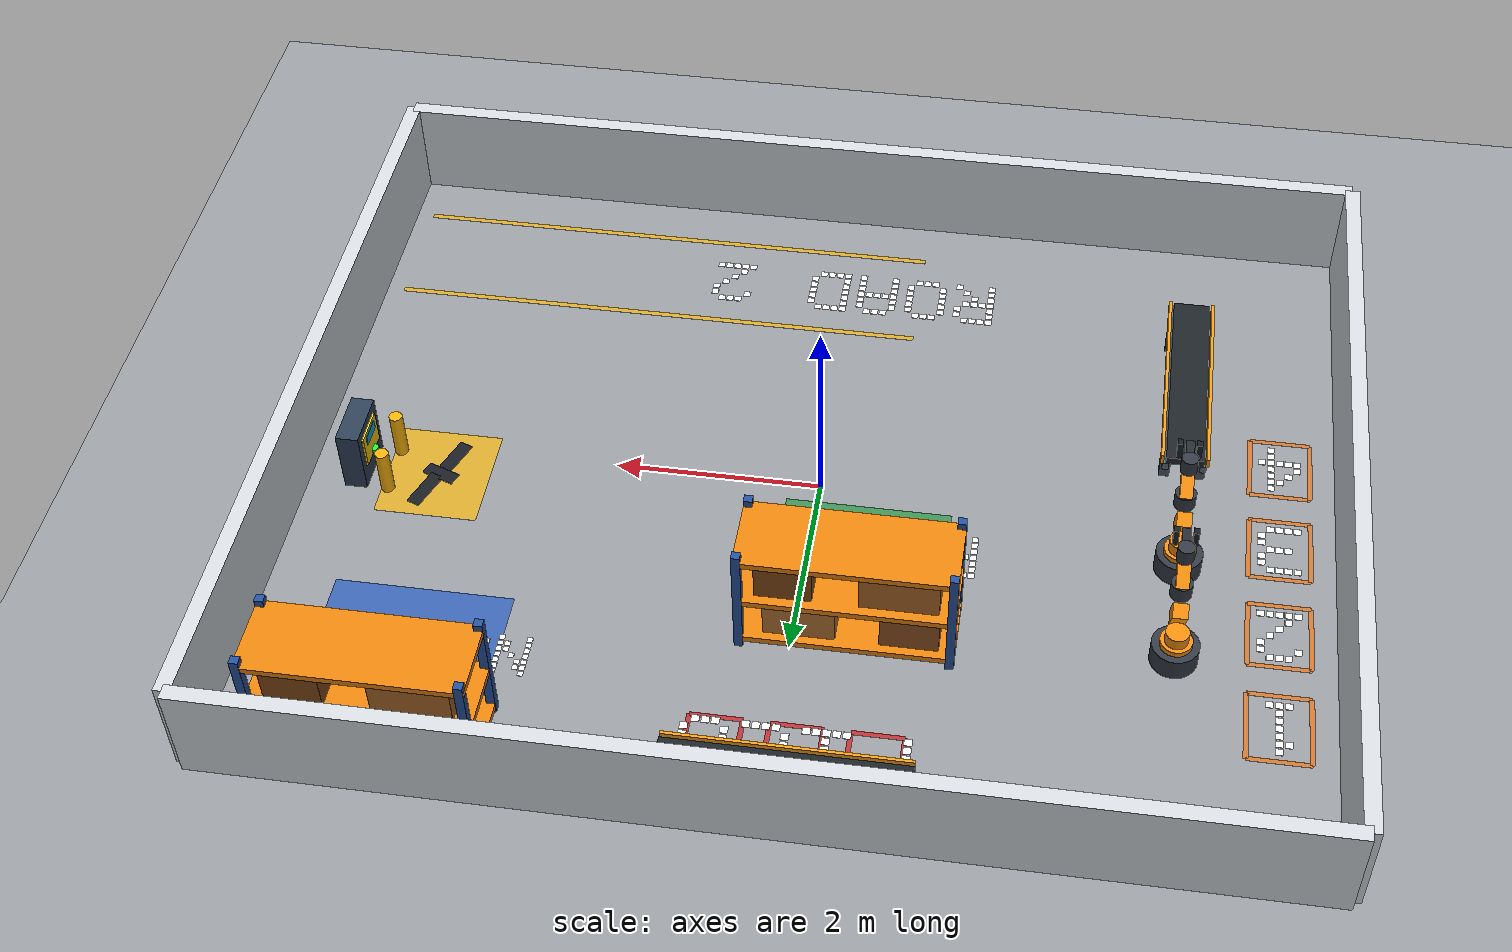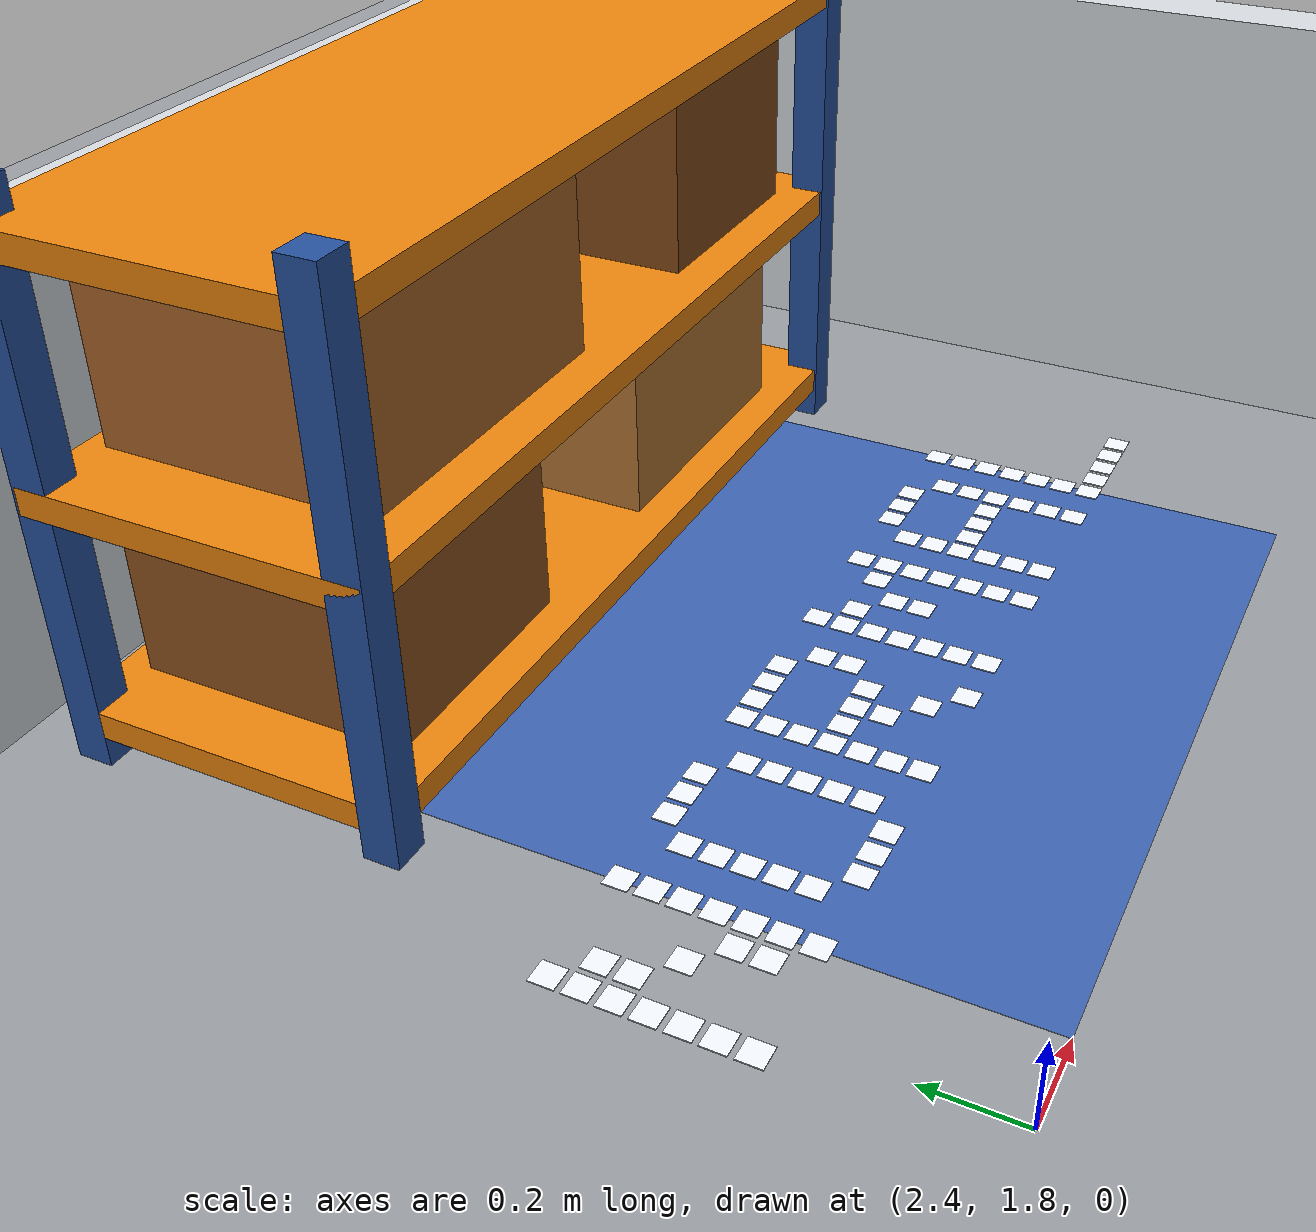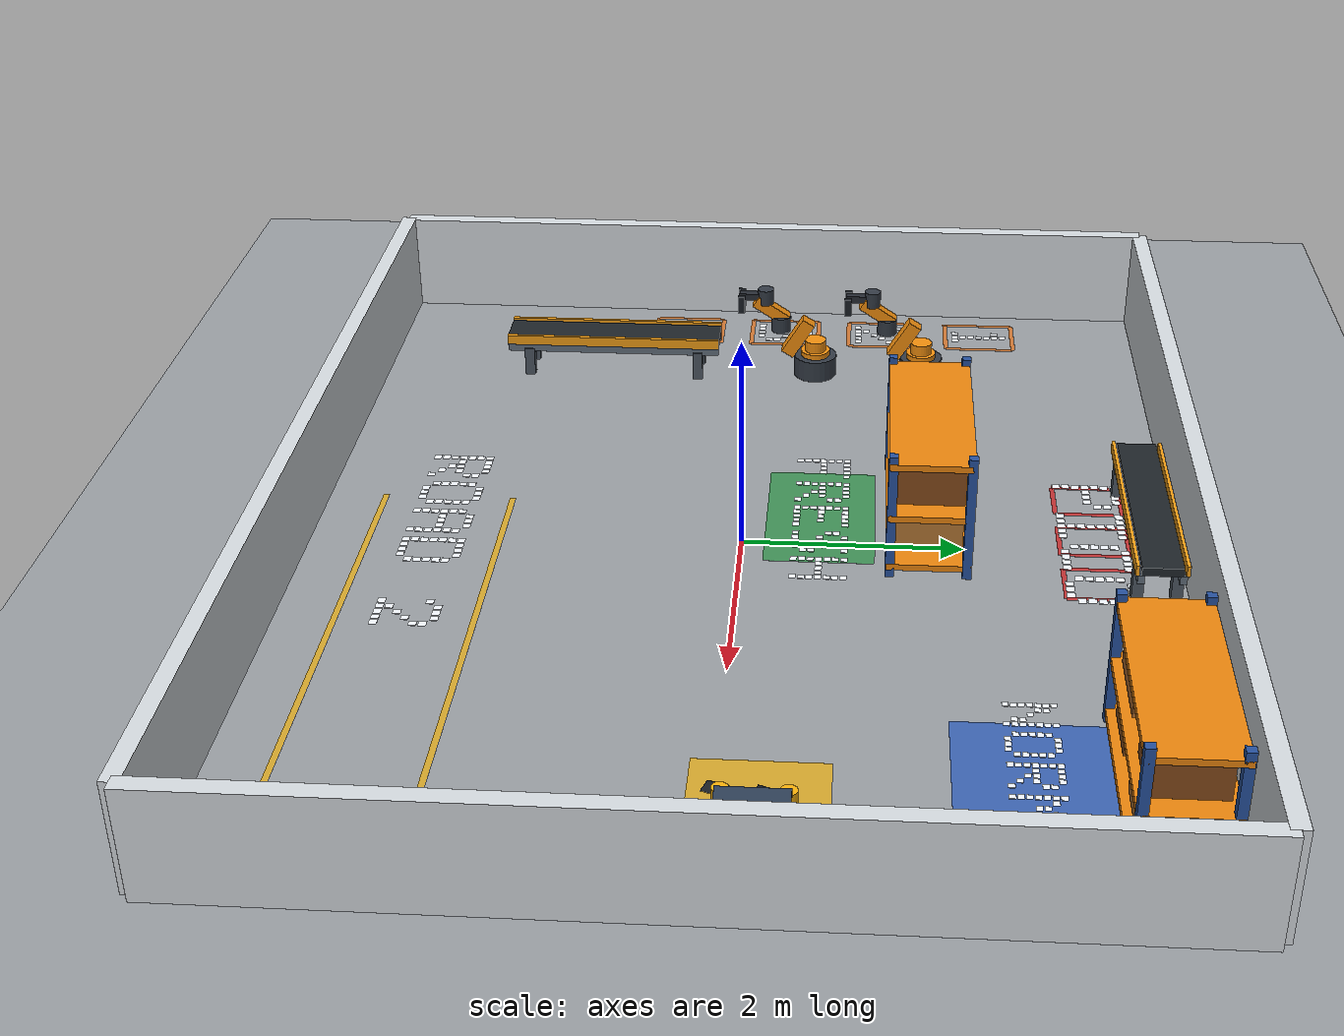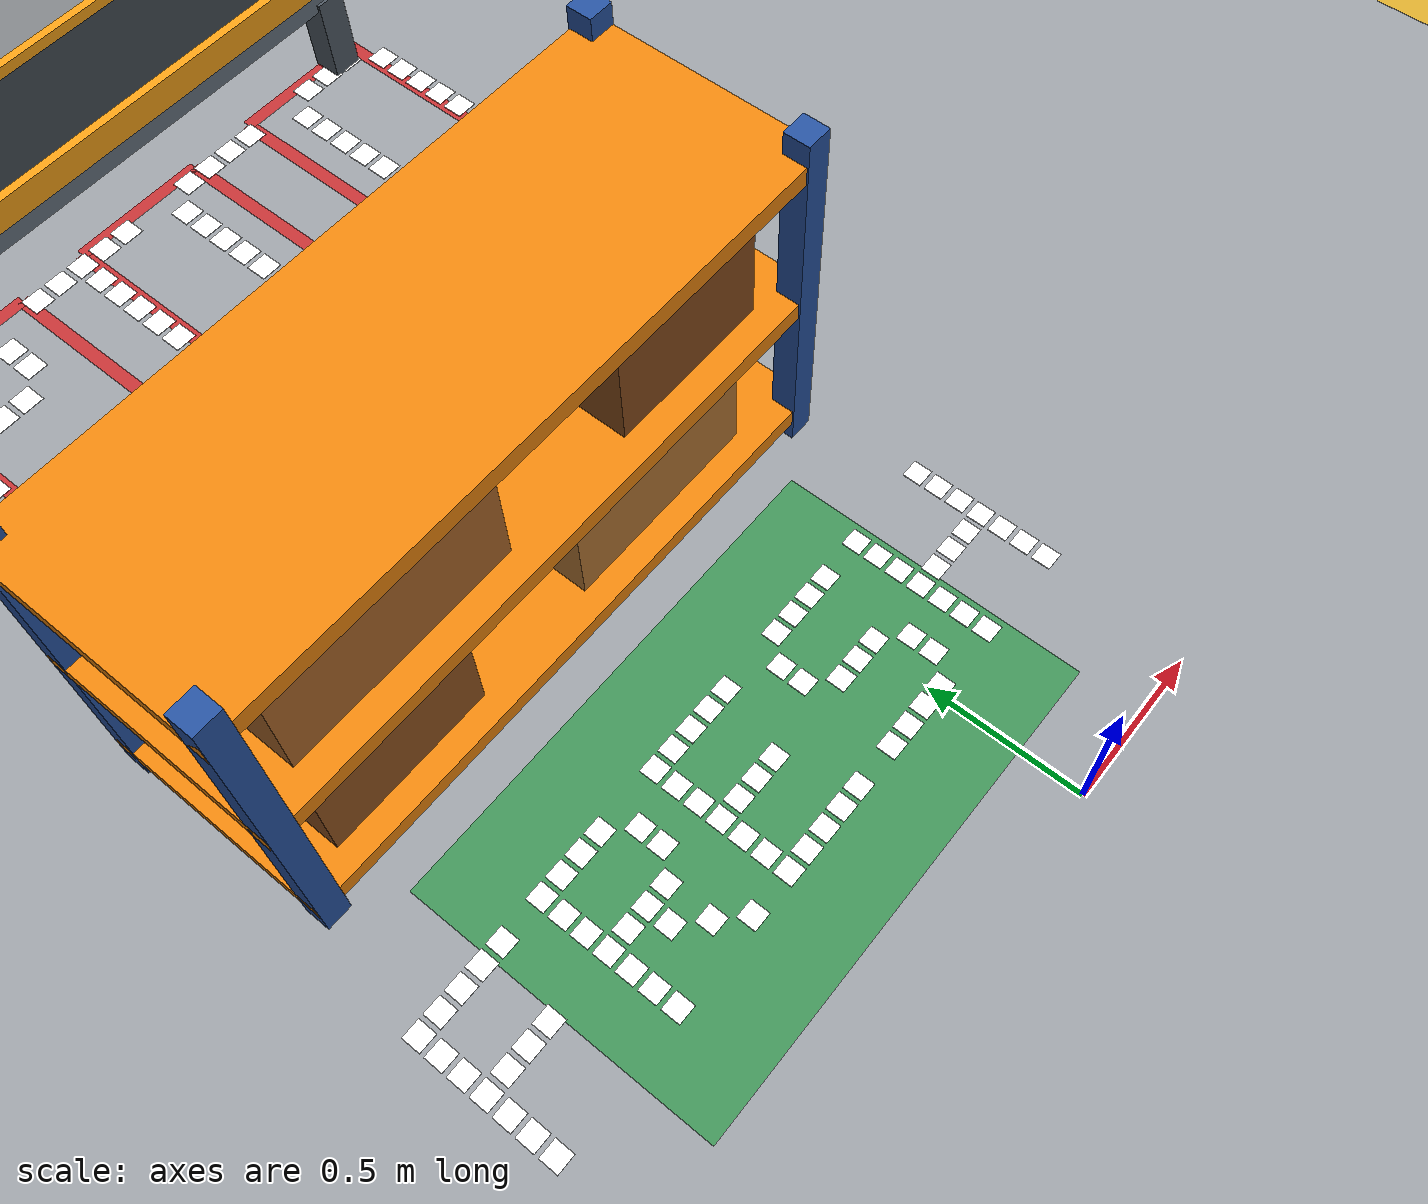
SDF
<?xml version="1.0"?>
<sdf version="1.8">
  <world name="mentorpi_warehouse">
    <physics name="1ms" type="ignored">
      <max_step_size>0.001</max_step_size>
      <real_time_factor>1.0</real_time_factor>
    </physics>

    <plugin filename="gz-sim-physics-system"
            name="gz::sim::systems::Physics"/>
    <plugin filename="gz-sim-user-commands-system"
            name="gz::sim::systems::UserCommands"/>
    <plugin filename="gz-sim-scene-broadcaster-system"
            name="gz::sim::systems::SceneBroadcaster"/>
    <plugin filename="gz-sim-sensors-system"
            name="gz::sim::systems::Sensors">
      <render_engine>ogre2</render_engine>
    </plugin>
    <plugin filename="gz-sim-imu-system"
            name="gz::sim::systems::Imu"/>
    <scene>
      <ambient>0.62 0.64 0.68 1</ambient>
      <background>0.72 0.80 0.88 1</background>
      <shadows>true</shadows>
    </scene>
    <light name="sun" type="directional">
      <cast_shadows>true</cast_shadows>
      <pose>0 0 8 0 0 0</pose>
      <diffuse>0.92 0.92 0.90 1</diffuse>
      <specular>0.25 0.25 0.25 1</specular>
      <attenuation>
        <range>30</range>
        <constant>0.9</constant>
        <linear>0.01</linear>
        <quadratic>0.001</quadratic>
      </attenuation>
      <direction>-0.35 0.25 -1</direction>
    </light>

    <model name="ground">
      <static>true</static>
      <link name="ground_link">
        <collision name="ground_collision">
          <geometry>
            <plane>
              <normal>0 0 1</normal>
              <size>12 10</size>
            </plane>
          </geometry>
          <surface>
            <friction>
              <ode>
                <mu>50</mu>
                <mu2>50</mu2>
              </ode>
            </friction>
          </surface>
        </collision>
        <visual name="ground_visual">
          <geometry>
            <plane>
              <normal>0 0 1</normal>
              <size>12 10</size>
            </plane>
          </geometry>
          <material>
            <ambient>0.48 0.50 0.52 1</ambient>
            <diffuse>0.60 0.62 0.64 1</diffuse>
            <specular>0.08 0.08 0.08 1</specular>
          </material>
        </visual>
      </link>
    </model>

    <model name="warehouse_walls">
      <static>true</static>
      <link name="walls">
        <collision name="north">
          <pose>0 4 0.5 0 0 0</pose>
          <geometry><box><size>10 0.15 1</size></box></geometry>
        </collision>
        <visual name="north_visual">
          <pose>0 4 0.5 0 0 0</pose>
          <geometry><box><size>10 0.15 1</size></box></geometry>
          <material><diffuse>0.84 0.86 0.88 1</diffuse></material>
        </visual>
        <collision name="south">
          <pose>0 -4 0.5 0 0 0</pose>
          <geometry><box><size>10 0.15 1</size></box></geometry>
        </collision>
        <visual name="south_visual">
          <pose>0 -4 0.5 0 0 0</pose>
          <geometry><box><size>10 0.15 1</size></box></geometry>
          <material><diffuse>0.84 0.86 0.88 1</diffuse></material>
        </visual>
        <collision name="east">
          <pose>5 0 0.5 0 0 0</pose>
          <geometry><box><size>0.15 8 1</size></box></geometry>
        </collision>
        <visual name="east_visual">
          <pose>5 0 0.5 0 0 0</pose>
          <geometry><box><size>0.15 8 1</size></box></geometry>
          <material><diffuse>0.84 0.86 0.88 1</diffuse></material>
        </visual>
        <collision name="west">
          <pose>-5 0 0.5 0 0 0</pose>
          <geometry><box><size>0.15 8 1</size></box></geometry>
        </collision>
        <visual name="west_visual">
          <pose>-5 0 0.5 0 0 0</pose>
          <geometry><box><size>0.15 8 1</size></box></geometry>
          <material><diffuse>0.84 0.86 0.88 1</diffuse></material>
        </visual>
      </link>
    </model>

    <include>
      <uri>model://warehouse_conveyor</uri>
      <name>left_conveyor</name>
      <pose>-3.45 -1.55 0 0 0 1.5708</pose>
    </include>
    <include>
      <uri>model://warehouse_conveyor</uri>
      <name>pico_conveyor</name>
      <pose>-0.20 3.64 0 0 0 0</pose>
    </include>

    <include>
      <uri>model://warehouse_robot_arm</uri>
      <name>robot_arm_upper</name>
      <pose>-3.45 1.65 0 0 0 -1.5708</pose>
    </include>
    <include>
      <uri>model://warehouse_robot_arm</uri>
      <name>robot_arm_lower</name>
      <pose>-3.45 0.55 0 0 0 -1.5708</pose>
    </include>

    <include>
      <uri>model://warehouse_charger</uri>
      <name>charging_station</name>
      <pose>4.45 0.35 0 0 0 1.5708</pose>
    </include>

    <include>
      <uri>model://warehouse_rack</uri>
      <name>fresh_rack</name>
      <pose>-0.50 1.67 0 0 0 0</pose>
    </include>
    <include>
      <uri>model://warehouse_rack</uri>
      <name>normal_rack</name>
      <pose>3.45 3.40 0 0 0 0</pose>
    </include>

    <include>
      <uri>model://warehouse_markings</uri>
      <name>floor_markings</name>
      <pose>0 0 0 0 0 0</pose>
    </include>

    <plugin filename="mentorpi_warehouse_pallet_manager"
            name="mentorpi_gz_sim::WarehousePalletManager">
      <command_service>/warehouse/pallet/command</command_service>
      <template_dir>pallet</template_dir>
      <spawn_bounds>-4.5 4.5 -3.5 3.5</spawn_bounds>
      <default_spawn_pose>-2.5 -2.8 0 0 0 0</default_spawn_pose>
      <linear_stop_threshold>0.02</linear_stop_threshold>
      <angular_stop_threshold>0.05</angular_stop_threshold>
      <default_pallet id="pallet_01" kind="fresh" state="loaded"
                      pose="-1.0 0.6 0 0 0 0"/>
      <default_pallet id="pallet_02" kind="fresh" state="loaded"
                      pose="-0.5 0.6 0 0 0 0"/>
      <default_pallet id="pallet_03" kind="fresh" state="loaded"
                      pose="0.0 0.6 0 0 0 0"/>
      <default_pallet id="pallet_04" kind="normal" state="loaded"
                      pose="2.9 2.4 0 0 0 0"/>
      <default_pallet id="pallet_05" kind="normal" state="loaded"
                      pose="3.4 2.4 0 0 0 0"/>
      <default_pallet id="pallet_06" kind="normal" state="loaded"
                      pose="3.9 2.4 0 0 0 0"/>
    </plugin>
  </world>
</sdf>

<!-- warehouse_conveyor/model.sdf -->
<sdf version="1.8">
  <model name="warehouse_conveyor">
    <static>true</static>
    <link name="conveyor">
      <collision name="conveyor_envelope">
        <pose>0 0 0.225 0 0 0</pose>
        <geometry>
          <box>
            <size>2.2 0.45 0.45</size>
          </box>
        </geometry>
      </collision>

      <visual name="belt">
        <pose>0 0 0.39 0 0 0</pose>
        <geometry>
          <box>
            <size>2.2 0.36 0.08</size>
          </box>
        </geometry>
        <material>
          <ambient>0.08 0.10 0.12 1</ambient>
          <diffuse>0.12 0.14 0.16 1</diffuse>
          <specular>0.25 0.25 0.25 1</specular>
        </material>
      </visual>
      <visual name="left_guard">
        <pose>0 0.215 0.40 0 0 0</pose>
        <geometry>
          <box>
            <size>2.2 0.03 0.10</size>
          </box>
        </geometry>
        <material>
          <ambient>0.85 0.50 0.05 1</ambient>
          <diffuse>0.95 0.62 0.08 1</diffuse>
        </material>
      </visual>
      <visual name="right_guard">
        <pose>0 -0.215 0.40 0 0 0</pose>
        <geometry>
          <box>
            <size>2.2 0.03 0.10</size>
          </box>
        </geometry>
        <material>
          <ambient>0.85 0.50 0.05 1</ambient>
          <diffuse>0.95 0.62 0.08 1</diffuse>
        </material>
      </visual>
      <visual name="frame_left">
        <pose>0 0.18 0.31 0 0 0</pose>
        <geometry>
          <box>
            <size>2.2 0.06 0.08</size>
          </box>
        </geometry>
        <material>
          <ambient>0.24 0.28 0.31 1</ambient>
          <diffuse>0.38 0.43 0.48 1</diffuse>
        </material>
      </visual>
      <visual name="frame_right">
        <pose>0 -0.18 0.31 0 0 0</pose>
        <geometry>
          <box>
            <size>2.2 0.06 0.08</size>
          </box>
        </geometry>
        <material>
          <ambient>0.24 0.28 0.31 1</ambient>
          <diffuse>0.38 0.43 0.48 1</diffuse>
        </material>
      </visual>
      <visual name="leg_front_left">
        <pose>0.88 0.17 0.15 0 0 0</pose>
        <geometry>
          <box>
            <size>0.10 0.10 0.30</size>
          </box>
        </geometry>
        <material>
          <diffuse>0.30 0.34 0.38 1</diffuse>
        </material>
      </visual>
      <visual name="leg_front_right">
        <pose>0.88 -0.17 0.15 0 0 0</pose>
        <geometry>
          <box>
            <size>0.10 0.10 0.30</size>
          </box>
        </geometry>
        <material>
          <diffuse>0.30 0.34 0.38 1</diffuse>
        </material>
      </visual>
      <visual name="leg_rear_left">
        <pose>-0.88 0.17 0.15 0 0 0</pose>
        <geometry>
          <box>
            <size>0.10 0.10 0.30</size>
          </box>
        </geometry>
        <material>
          <diffuse>0.30 0.34 0.38 1</diffuse>
        </material>
      </visual>
      <visual name="leg_rear_right">
        <pose>-0.88 -0.17 0.15 0 0 0</pose>
        <geometry>
          <box>
            <size>0.10 0.10 0.30</size>
          </box>
        </geometry>
        <material>
          <diffuse>0.30 0.34 0.38 1</diffuse>
        </material>
      </visual>
    </link>
  </model>
</sdf>

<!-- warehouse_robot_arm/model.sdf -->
<sdf version="1.8">
  <model name="warehouse_robot_arm">
    <static>true</static>
    <link name="base_link">
      <collision name="base_collision">
        <pose>0 0 0.11 0 0 0</pose>
        <geometry>
          <cylinder>
            <radius>0.22</radius>
            <length>0.22</length>
          </cylinder>
        </geometry>
      </collision>
      <visual name="base">
        <pose>0 0 0.11 0 0 0</pose>
        <geometry>
          <cylinder>
            <radius>0.22</radius>
            <length>0.22</length>
          </cylinder>
        </geometry>
        <material>
          <ambient>0.12 0.14 0.17 1</ambient>
          <diffuse>0.20 0.23 0.27 1</diffuse>
        </material>
      </visual>
      <visual name="turntable">
        <pose>0 0 0.235 0 0 0</pose>
        <geometry>
          <cylinder>
            <radius>0.15</radius>
            <length>0.08</length>
          </cylinder>
        </geometry>
        <material>
          <ambient>0.85 0.45 0.03 1</ambient>
          <diffuse>0.95 0.56 0.05 1</diffuse>
        </material>
      </visual>
    </link>

    <link name="shoulder_link">
      <pose>0 0 0.30 0 0 0</pose>
      <collision name="shoulder_collision">
        <pose>0.18 0 0.12 0 1.02 0</pose>
        <geometry>
          <box>
            <size>0.42 0.14 0.14</size>
          </box>
        </geometry>
      </collision>
      <visual name="shoulder_joint">
        <geometry>
          <cylinder>
            <radius>0.11</radius>
            <length>0.18</length>
          </cylinder>
        </geometry>
        <material>
          <diffuse>0.95 0.56 0.05 1</diffuse>
        </material>
      </visual>
      <visual name="shoulder_body">
        <pose>0.18 0 0.12 0 1.02 0</pose>
        <geometry>
          <box>
            <size>0.42 0.14 0.14</size>
          </box>
        </geometry>
        <material>
          <diffuse>0.95 0.56 0.05 1</diffuse>
        </material>
      </visual>
    </link>

    <link name="forearm_link">
      <pose>0.36 0 0.57 0 0 0</pose>
      <collision name="forearm_collision">
        <pose>0.10 0 0.15 0 -0.58 0</pose>
        <geometry>
          <box>
            <size>0.38 0.12 0.12</size>
          </box>
        </geometry>
      </collision>
      <visual name="elbow_joint">
        <geometry>
          <cylinder>
            <radius>0.10</radius>
            <length>0.16</length>
          </cylinder>
        </geometry>
        <material>
          <diffuse>0.20 0.23 0.27 1</diffuse>
        </material>
      </visual>
      <visual name="forearm_body">
        <pose>0.10 0 0.15 0 -0.58 0</pose>
        <geometry>
          <box>
            <size>0.38 0.12 0.12</size>
          </box>
        </geometry>
        <material>
          <diffuse>0.95 0.56 0.05 1</diffuse>
        </material>
      </visual>
    </link>

    <link name="tool_link">
      <pose>0.52 0 0.87 0 0 0</pose>
      <collision name="tool_collision">
        <geometry>
          <box>
            <size>0.34 0.18 0.10</size>
          </box>
        </geometry>
      </collision>
      <visual name="wrist">
        <geometry>
          <cylinder>
            <radius>0.08</radius>
            <length>0.16</length>
          </cylinder>
        </geometry>
        <material>
          <diffuse>0.20 0.23 0.27 1</diffuse>
        </material>
      </visual>
      <visual name="gripper_bar">
        <pose>0.13 0 0 0 0 0</pose>
        <geometry>
          <box>
            <size>0.28 0.08 0.07</size>
          </box>
        </geometry>
        <material>
          <diffuse>0.15 0.17 0.20 1</diffuse>
        </material>
      </visual>
      <visual name="gripper_left">
        <pose>0.25 0.09 -0.06 0 0 0</pose>
        <geometry>
          <box>
            <size>0.07 0.05 0.18</size>
          </box>
        </geometry>
        <material>
          <diffuse>0.10 0.12 0.14 1</diffuse>
        </material>
      </visual>
      <visual name="gripper_right">
        <pose>0.25 -0.09 -0.06 0 0 0</pose>
        <geometry>
          <box>
            <size>0.07 0.05 0.18</size>
          </box>
        </geometry>
        <material>
          <diffuse>0.10 0.12 0.14 1</diffuse>
        </material>
      </visual>
    </link>

    <joint name="base_to_shoulder" type="fixed">
      <parent>base_link</parent>
      <child>shoulder_link</child>
    </joint>
    <joint name="shoulder_to_forearm" type="fixed">
      <parent>shoulder_link</parent>
      <child>forearm_link</child>
    </joint>
    <joint name="forearm_to_tool" type="fixed">
      <parent>forearm_link</parent>
      <child>tool_link</child>
    </joint>
  </model>
</sdf>

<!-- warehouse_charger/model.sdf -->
<sdf version="1.8">
  <model name="warehouse_charger">
    <static>true</static>
    <link name="charger">
      <collision name="cabinet_collision">
        <pose>0 0 0.325 0 0 0</pose>
        <geometry>
          <box>
            <size>0.55 0.22 0.65</size>
          </box>
        </geometry>
      </collision>
      <collision name="left_bollard_collision">
        <pose>0.25 0.31 0.24 0 0 0</pose>
        <geometry>
          <cylinder>
            <radius>0.065</radius>
            <length>0.48</length>
          </cylinder>
        </geometry>
      </collision>
      <collision name="right_bollard_collision">
        <pose>-0.25 0.31 0.24 0 0 0</pose>
        <geometry>
          <cylinder>
            <radius>0.065</radius>
            <length>0.48</length>
          </cylinder>
        </geometry>
      </collision>

      <visual name="cabinet">
        <pose>0 0 0.325 0 0 0</pose>
        <geometry>
          <box>
            <size>0.55 0.22 0.65</size>
          </box>
        </geometry>
        <material>
          <ambient>0.12 0.16 0.22 1</ambient>
          <diffuse>0.18 0.25 0.34 1</diffuse>
        </material>
      </visual>
      <visual name="front_panel">
        <pose>0 0.116 0.39 0 0 0</pose>
        <geometry>
          <box>
            <size>0.38 0.025 0.34</size>
          </box>
        </geometry>
        <material>
          <ambient>0.95 0.72 0.05 1</ambient>
          <diffuse>1.0 0.82 0.08 1</diffuse>
          <emissive>0.18 0.12 0.01 1</emissive>
        </material>
      </visual>
      <visual name="display">
        <pose>0 0.131 0.48 0 0 0</pose>
        <geometry>
          <box>
            <size>0.24 0.012 0.10</size>
          </box>
        </geometry>
        <material>
          <diffuse>0.05 0.65 0.85 1</diffuse>
          <emissive>0.02 0.30 0.45 1</emissive>
        </material>
      </visual>
      <visual name="status_light">
        <pose>0 0.14 0.27 0 0 0</pose>
        <geometry>
          <cylinder>
            <radius>0.045</radius>
            <length>0.025</length>
          </cylinder>
        </geometry>
        <material>
          <diffuse>0.10 0.95 0.25 1</diffuse>
          <emissive>0.04 0.50 0.10 1</emissive>
        </material>
      </visual>
      <visual name="left_bollard">
        <pose>0.25 0.31 0.24 0 0 0</pose>
        <geometry>
          <cylinder>
            <radius>0.065</radius>
            <length>0.48</length>
          </cylinder>
        </geometry>
        <material>
          <diffuse>0.98 0.70 0.04 1</diffuse>
        </material>
      </visual>
      <visual name="right_bollard">
        <pose>-0.25 0.31 0.24 0 0 0</pose>
        <geometry>
          <cylinder>
            <radius>0.065</radius>
            <length>0.48</length>
          </cylinder>
        </geometry>
        <material>
          <diffuse>0.98 0.70 0.04 1</diffuse>
        </material>
      </visual>
    </link>
  </model>
</sdf>

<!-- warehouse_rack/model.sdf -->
<sdf version="1.8">
  <model name="warehouse_rack">
    <static>true</static>
    <link name="rack">
      <collision name="rack_envelope">
        <pose>0 0 0.6 0 0 0</pose>
        <geometry>
          <box>
            <size>2.0 0.75 1.2</size>
          </box>
        </geometry>
      </collision>

      <visual name="post_front_left">
        <pose>-0.96 -0.34 0.6 0 0 0</pose>
        <geometry><box><size>0.08 0.08 1.2</size></box></geometry>
        <material><diffuse>0.15 0.32 0.62 1</diffuse></material>
      </visual>
      <visual name="post_front_right">
        <pose>0.96 -0.34 0.6 0 0 0</pose>
        <geometry><box><size>0.08 0.08 1.2</size></box></geometry>
        <material><diffuse>0.15 0.32 0.62 1</diffuse></material>
      </visual>
      <visual name="post_rear_left">
        <pose>-0.96 0.34 0.6 0 0 0</pose>
        <geometry><box><size>0.08 0.08 1.2</size></box></geometry>
        <material><diffuse>0.15 0.32 0.62 1</diffuse></material>
      </visual>
      <visual name="post_rear_right">
        <pose>0.96 0.34 0.6 0 0 0</pose>
        <geometry><box><size>0.08 0.08 1.2</size></box></geometry>
        <material><diffuse>0.15 0.32 0.62 1</diffuse></material>
      </visual>

      <visual name="shelf_lower">
        <pose>0 0 0.10 0 0 0</pose>
        <geometry><box><size>2.0 0.75 0.06</size></box></geometry>
        <material><diffuse>0.92 0.52 0.05 1</diffuse></material>
      </visual>
      <visual name="shelf_middle">
        <pose>0 0 0.59 0 0 0</pose>
        <geometry><box><size>2.0 0.75 0.06</size></box></geometry>
        <material><diffuse>0.92 0.52 0.05 1</diffuse></material>
      </visual>
      <visual name="shelf_upper">
        <pose>0 0 1.10 0 0 0</pose>
        <geometry><box><size>2.0 0.75 0.06</size></box></geometry>
        <material><diffuse>0.92 0.52 0.05 1</diffuse></material>
      </visual>

      <visual name="carton_lower_left">
        <pose>-0.58 0 0.34 0 0 0</pose>
        <geometry><box><size>0.54 0.60 0.40</size></box></geometry>
        <material><diffuse>0.56 0.32 0.12 1</diffuse></material>
      </visual>
      <visual name="carton_lower_right">
        <pose>0.42 0 0.34 0 0 0</pose>
        <geometry><box><size>0.66 0.60 0.40</size></box></geometry>
        <material><diffuse>0.70 0.46 0.20 1</diffuse></material>
      </visual>
      <visual name="carton_upper_left">
        <pose>-0.48 0 0.84 0 0 0</pose>
        <geometry><box><size>0.72 0.60 0.40</size></box></geometry>
        <material><diffuse>0.66 0.40 0.16 1</diffuse></material>
      </visual>
      <visual name="carton_upper_right">
        <pose>0.56 0 0.84 0 0 0</pose>
        <geometry><box><size>0.52 0.60 0.40</size></box></geometry>
        <material><diffuse>0.52 0.29 0.10 1</diffuse></material>
      </visual>
    </link>
  </model>
</sdf>

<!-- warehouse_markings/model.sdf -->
<sdf version="1.8">
  <model name="warehouse_markings">
    <static>true</static>
    <link name="markings">
      <visual name="fresh_zone">
        <pose>-0.5 0.7 0.001 0 0 0</pose>
        <geometry>
          <box>
            <size>1.6 1 0.002</size>
          </box>
        </geometry>
        <material>
          <ambient>0.08 0.58 0.20 0.62</ambient>
          <diffuse>0.08 0.58 0.20 0.62</diffuse>
        </material>
      </visual>
      <visual name="fresh_label_pixel_000">
        <pose>-1.55 0.925 0.003 0 0 0</pose>
        <geometry>
          <box>
            <size>0.0615 0.0615 0.002</size>
          </box>
        </geometry>
        <material>
          <ambient>0.96 0.98 1.0 1</ambient>
          <diffuse>0.96 0.98 1.0 1</diffuse>
        </material>
      </visual>
      <visual name="fresh_label_pixel_001">
        <pose>-1.475 0.925 0.003 0 0 0</pose>
        <geometry>
          <box>
            <size>0.0615 0.0615 0.002</size>
          </box>
        </geometry>
        <material>
          <ambient>0.96 0.98 1.0 1</ambient>
          <diffuse>0.96 0.98 1.0 1</diffuse>
        </material>
      </visual>
      <visual name="fresh_label_pixel_002">
        <pose>-1.4 0.925 0.003 0 0 0</pose>
        <geometry>
          <box>
            <size>0.0615 0.0615 0.002</size>
          </box>
        </geometry>
        <material>
          <ambient>0.96 0.98 1.0 1</ambient>
          <diffuse>0.96 0.98 1.0 1</diffuse>
        </material>
      </visual>
      <visual name="fresh_label_pixel_003">
        <pose>-1.325 0.925 0.003 0 0 0</pose>
        <geometry>
          <box>
            <size>0.0615 0.0615 0.002</size>
          </box>
        </geometry>
        <material>
          <ambient>0.96 0.98 1.0 1</ambient>
          <diffuse>0.96 0.98 1.0 1</diffuse>
        </material>
      </visual>
      <visual name="fresh_label_pixel_004">
        <pose>-1.25 0.925 0.003 0 0 0</pose>
        <geometry>
          <box>
            <size>0.0615 0.0615 0.002</size>
          </box>
        </geometry>
        <material>
          <ambient>0.96 0.98 1.0 1</ambient>
          <diffuse>0.96 0.98 1.0 1</diffuse>
        </material>
      </visual>
      <visual name="fresh_label_pixel_005">
        <pose>-1.55 0.85 0.003 0 0 0</pose>
        <geometry>
          <box>
            <size>0.0615 0.0615 0.002</size>
          </box>
        </geometry>
        <material>
          <ambient>0.96 0.98 1.0 1</ambient>
          <diffuse>0.96 0.98 1.0 1</diffuse>
        </material>
      </visual>
      <visual name="fresh_label_pixel_006">
        <pose>-1.55 0.775 0.003 0 0 0</pose>
        <geometry>
          <box>
            <size>0.0615 0.0615 0.002</size>
          </box>
        </geometry>
        <material>
          <ambient>0.96 0.98 1.0 1</ambient>
          <diffuse>0.96 0.98 1.0 1</diffuse>
        </material>
      </visual>
      <visual name="fresh_label_pixel_007">
        <pose>-1.55 0.7 0.003 0 0 0</pose>
        <geometry>
          <box>
            <size>0.0615 0.0615 0.002</size>
          </box>
        </geometry>
        <material>
          <ambient>0.96 0.98 1.0 1</ambient>
          <diffuse>0.96 0.98 1.0 1</diffuse>
        </material>
      </visual>
      <visual name="fresh_label_pixel_008">
        <pose>-1.475 0.7 0.003 0 0 0</pose>
        <geometry>
          <box>
            <size>0.0615 0.0615 0.002</size>
          </box>
        </geometry>
        <material>
          <ambient>0.96 0.98 1.0 1</ambient>
          <diffuse>0.96 0.98 1.0 1</diffuse>
        </material>
      </visual>
      <visual name="fresh_label_pixel_009">
        <pose>-1.4 0.7 0.003 0 0 0</pose>
        <geometry>
          <box>
            <size>0.0615 0.0615 0.002</size>
          </box>
        </geometry>
        <material>
          <ambient>0.96 0.98 1.0 1</ambient>
          <diffuse>0.96 0.98 1.0 1</diffuse>
        </material>
      </visual>
      <visual name="fresh_label_pixel_010">
        <pose>-1.325 0.7 0.003 0 0 0</pose>
        <geometry>
          <box>
            <size>0.0615 0.0615 0.002</size>
          </box>
        </geometry>
        <material>
          <ambient>0.96 0.98 1.0 1</ambient>
          <diffuse>0.96 0.98 1.0 1</diffuse>
        </material>
      </visual>
      <visual name="fresh_label_pixel_011">
        <pose>-1.55 0.625 0.003 0 0 0</pose>
        <geometry>
          <box>
            <size>0.0615 0.0615 0.002</size>
          </box>
        </geometry>
        <material>
          <ambient>0.96 0.98 1.0 1</ambient>
          <diffuse>0.96 0.98 1.0 1</diffuse>
        </material>
      </visual>
      <visual name="fresh_label_pixel_012">
        <pose>-1.55 0.55 0.003 0 0 0</pose>
        <geometry>
          <box>
            <size>0.0615 0.0615 0.002</size>
          </box>
        </geometry>
        <material>
          <ambient>0.96 0.98 1.0 1</ambient>
          <diffuse>0.96 0.98 1.0 1</diffuse>
        </material>
      </visual>
      <visual name="fresh_label_pixel_013">
        <pose>-1.55 0.475 0.003 0 0 0</pose>
        <geometry>
          <box>
            <size>0.0615 0.0615 0.002</size>
          </box>
        </geometry>
        <material>
          <ambient>0.96 0.98 1.0 1</ambient>
          <diffuse>0.96 0.98 1.0 1</diffuse>
        </material>
      </visual>
      <visual name="fresh_label_pixel_014">
        <pose>-1.1 0.925 0.003 0 0 0</pose>
        <geometry>
          <box>
            <size>0.0615 0.0615 0.002</size>
          </box>
        </geometry>
        <material>
          <ambient>0.96 0.98 1.0 1</ambient>
          <diffuse>0.96 0.98 1.0 1</diffuse>
        </material>
      </visual>
      <visual name="fresh_label_pixel_015">
        <pose>-1.025 0.925 0.003 0 0 0</pose>
        <geometry>
          <box>
            <size>0.0615 0.0615 0.002</size>
          </box>
        </geometry>
        <material>
          <ambient>0.96 0.98 1.0 1</ambient>
          <diffuse>0.96 0.98 1.0 1</diffuse>
        </material>
      </visual>
      <visual name="fresh_label_pixel_016">
        <pose>-0.95 0.925 0.003 0 0 0</pose>
        <geometry>
          <box>
            <size>0.0615 0.0615 0.002</size>
          </box>
        </geometry>
        <material>
          <ambient>0.96 0.98 1.0 1</ambient>
          <diffuse>0.96 0.98 1.0 1</diffuse>
        </material>
      </visual>
      <visual name="fresh_label_pixel_017">
        <pose>-0.875 0.925 0.003 0 0 0</pose>
        <geometry>
          <box>
            <size>0.0615 0.0615 0.002</size>
          </box>
        </geometry>
        <material>
          <ambient>0.96 0.98 1.0 1</ambient>
          <diffuse>0.96 0.98 1.0 1</diffuse>
        </material>
      </visual>
      <visual name="fresh_label_pixel_018">
        <pose>-1.1 0.85 0.003 0 0 0</pose>
        <geometry>
          <box>
            <size>0.0615 0.0615 0.002</size>
          </box>
        </geometry>
        <material>
          <ambient>0.96 0.98 1.0 1</ambient>
          <diffuse>0.96 0.98 1.0 1</diffuse>
        </material>
      </visual>
      <visual name="fresh_label_pixel_019">
        <pose>-0.8 0.85 0.003 0 0 0</pose>
        <geometry>
          <box>
            <size>0.0615 0.0615 0.002</size>
          </box>
        </geometry>
        <material>
          <ambient>0.96 0.98 1.0 1</ambient>
          <diffuse>0.96 0.98 1.0 1</diffuse>
        </material>
      </visual>
      <visual name="fresh_label_pixel_020">
        <pose>-1.1 0.775 0.003 0 0 0</pose>
        <geometry>
          <box>
            <size>0.0615 0.0615 0.002</size>
          </box>
        </geometry>
        <material>
          <ambient>0.96 0.98 1.0 1</ambient>
          <diffuse>0.96 0.98 1.0 1</diffuse>
        </material>
      </visual>
      <visual name="fresh_label_pixel_021">
        <pose>-0.8 0.775 0.003 0 0 0</pose>
        <geometry>
          <box>
            <size>0.0615 0.0615 0.002</size>
          </box>
        </geometry>
        <material>
          <ambient>0.96 0.98 1.0 1</ambient>
          <diffuse>0.96 0.98 1.0 1</diffuse>
        </material>
      </visual>
      <visual name="fresh_label_pixel_022">
        <pose>-1.1 0.7 0.003 0 0 0</pose>
        <geometry>
          <box>
            <size>0.0615 0.0615 0.002</size>
          </box>
        </geometry>
        <material>
          <ambient>0.96 0.98 1.0 1</ambient>
          <diffuse>0.96 0.98 1.0 1</diffuse>
        </material>
      </visual>
      <visual name="fresh_label_pixel_023">
        <pose>-1.025 0.7 0.003 0 0 0</pose>
        <geometry>
          <box>
            <size>0.0615 0.0615 0.002</size>
          </box>
        </geometry>
        <material>
          <ambient>0.96 0.98 1.0 1</ambient>
          <diffuse>0.96 0.98 1.0 1</diffuse>
        </material>
      </visual>
      <visual name="fresh_label_pixel_024">
        <pose>-0.95 0.7 0.003 0 0 0</pose>
        <geometry>
          <box>
            <size>0.0615 0.0615 0.002</size>
          </box>
        </geometry>
        <material>
          <ambient>0.96 0.98 1.0 1</ambient>
          <diffuse>0.96 0.98 1.0 1</diffuse>
        </material>
      </visual>
      <visual name="fresh_label_pixel_025">
        <pose>-0.875 0.7 0.003 0 0 0</pose>
        <geometry>
          <box>
            <size>0.0615 0.0615 0.002</size>
          </box>
        </geometry>
        <material>
          <ambient>0.96 0.98 1.0 1</ambient>
          <diffuse>0.96 0.98 1.0 1</diffuse>
        </material>
      </visual>
      <visual name="fresh_label_pixel_026">
        <pose>-1.1 0.625 0.003 0 0 0</pose>
        <geometry>
          <box>
            <size>0.0615 0.0615 0.002</size>
          </box>
        </geometry>
        <material>
          <ambient>0.96 0.98 1.0 1</ambient>
          <diffuse>0.96 0.98 1.0 1</diffuse>
        </material>
      </visual>
      <visual name="fresh_label_pixel_027">
        <pose>-0.95 0.625 0.003 0 0 0</pose>
        <geometry>
          <box>
            <size>0.0615 0.0615 0.002</size>
          </box>
        </geometry>
        <material>
          <ambient>0.96 0.98 1.0 1</ambient>
          <diffuse>0.96 0.98 1.0 1</diffuse>
        </material>
      </visual>
      <visual name="fresh_label_pixel_028">
        <pose>-1.1 0.55 0.003 0 0 0</pose>
        <geometry>
          <box>
            <size>0.0615 0.0615 0.002</size>
          </box>
        </geometry>
        <material>
          <ambient>0.96 0.98 1.0 1</ambient>
          <diffuse>0.96 0.98 1.0 1</diffuse>
        </material>
      </visual>
      <visual name="fresh_label_pixel_029">
        <pose>-0.875 0.55 0.003 0 0 0</pose>
        <geometry>
          <box>
            <size>0.0615 0.0615 0.002</size>
          </box>
        </geometry>
        <material>
          <ambient>0.96 0.98 1.0 1</ambient>
          <diffuse>0.96 0.98 1.0 1</diffuse>
        </material>
      </visual>
      <visual name="fresh_label_pixel_030">
        <pose>-1.1 0.475 0.003 0 0 0</pose>
        <geometry>
          <box>
            <size>0.0615 0.0615 0.002</size>
          </box>
        </geometry>
        <material>
          <ambient>0.96 0.98 1.0 1</ambient>
          <diffuse>0.96 0.98 1.0 1</diffuse>
        </material>
      </visual>
      <visual name="fresh_label_pixel_031">
        <pose>-0.8 0.475 0.003 0 0 0</pose>
        <geometry>
          <box>
            <size>0.0615 0.0615 0.002</size>
          </box>
        </geometry>
        <material>
          <ambient>0.96 0.98 1.0 1</ambient>
          <diffuse>0.96 0.98 1.0 1</diffuse>
        </material>
      </visual>
      <visual name="fresh_label_pixel_032">
        <pose>-0.65 0.925 0.003 0 0 0</pose>
        <geometry>
          <box>
            <size>0.0615 0.0615 0.002</size>
          </box>
        </geometry>
        <material>
          <ambient>0.96 0.98 1.0 1</ambient>
          <diffuse>0.96 0.98 1.0 1</diffuse>
        </material>
      </visual>
      <visual name="fresh_label_pixel_033">
        <pose>-0.575 0.925 0.003 0 0 0</pose>
        <geometry>
          <box>
            <size>0.0615 0.0615 0.002</size>
          </box>
        </geometry>
        <material>
          <ambient>0.96 0.98 1.0 1</ambient>
          <diffuse>0.96 0.98 1.0 1</diffuse>
        </material>
      </visual>
      <visual name="fresh_label_pixel_034">
        <pose>-0.5 0.925 0.003 0 0 0</pose>
        <geometry>
          <box>
            <size>0.0615 0.0615 0.002</size>
          </box>
        </geometry>
        <material>
          <ambient>0.96 0.98 1.0 1</ambient>
          <diffuse>0.96 0.98 1.0 1</diffuse>
        </material>
      </visual>
      <visual name="fresh_label_pixel_035">
        <pose>-0.425 0.925 0.003 0 0 0</pose>
        <geometry>
          <box>
            <size>0.0615 0.0615 0.002</size>
          </box>
        </geometry>
        <material>
          <ambient>0.96 0.98 1.0 1</ambient>
          <diffuse>0.96 0.98 1.0 1</diffuse>
        </material>
      </visual>
      <visual name="fresh_label_pixel_036">
        <pose>-0.35 0.925 0.003 0 0 0</pose>
        <geometry>
          <box>
            <size>0.0615 0.0615 0.002</size>
          </box>
        </geometry>
        <material>
          <ambient>0.96 0.98 1.0 1</ambient>
          <diffuse>0.96 0.98 1.0 1</diffuse>
        </material>
      </visual>
      <visual name="fresh_label_pixel_037">
        <pose>-0.65 0.85 0.003 0 0 0</pose>
        <geometry>
          <box>
            <size>0.0615 0.0615 0.002</size>
          </box>
        </geometry>
        <material>
          <ambient>0.96 0.98 1.0 1</ambient>
          <diffuse>0.96 0.98 1.0 1</diffuse>
        </material>
      </visual>
      <visual name="fresh_label_pixel_038">
        <pose>-0.65 0.775 0.003 0 0 0</pose>
        <geometry>
          <box>
            <size>0.0615 0.0615 0.002</size>
          </box>
        </geometry>
        <material>
          <ambient>0.96 0.98 1.0 1</ambient>
          <diffuse>0.96 0.98 1.0 1</diffuse>
        </material>
      </visual>
      <visual name="fresh_label_pixel_039">
        <pose>-0.65 0.7 0.003 0 0 0</pose>
        <geometry>
          <box>
            <size>0.0615 0.0615 0.002</size>
          </box>
        </geometry>
        <material>
          <ambient>0.96 0.98 1.0 1</ambient>
          <diffuse>0.96 0.98 1.0 1</diffuse>
        </material>
      </visual>
      <visual name="fresh_label_pixel_040">
        <pose>-0.575 0.7 0.003 0 0 0</pose>
        <geometry>
          <box>
            <size>0.0615 0.0615 0.002</size>
          </box>
        </geometry>
        <material>
          <ambient>0.96 0.98 1.0 1</ambient>
          <diffuse>0.96 0.98 1.0 1</diffuse>
        </material>
      </visual>
      <visual name="fresh_label_pixel_041">
        <pose>-0.5 0.7 0.003 0 0 0</pose>
        <geometry>
          <box>
            <size>0.0615 0.0615 0.002</size>
          </box>
        </geometry>
        <material>
          <ambient>0.96 0.98 1.0 1</ambient>
          <diffuse>0.96 0.98 1.0 1</diffuse>
        </material>
      </visual>
      <visual name="fresh_label_pixel_042">
        <pose>-0.425 0.7 0.003 0 0 0</pose>
        <geometry>
          <box>
            <size>0.0615 0.0615 0.002</size>
          </box>
        </geometry>
        <material>
          <ambient>0.96 0.98 1.0 1</ambient>
          <diffuse>0.96 0.98 1.0 1</diffuse>
        </material>
      </visual>
      <visual name="fresh_label_pixel_043">
        <pose>-0.65 0.625 0.003 0 0 0</pose>
        <geometry>
          <box>
            <size>0.0615 0.0615 0.002</size>
          </box>
        </geometry>
        <material>
          <ambient>0.96 0.98 1.0 1</ambient>
          <diffuse>0.96 0.98 1.0 1</diffuse>
        </material>
      </visual>
      <visual name="fresh_label_pixel_044">
        <pose>-0.65 0.55 0.003 0 0 0</pose>
        <geometry>
          <box>
            <size>0.0615 0.0615 0.002</size>
          </box>
        </geometry>
        <material>
          <ambient>0.96 0.98 1.0 1</ambient>
          <diffuse>0.96 0.98 1.0 1</diffuse>
        </material>
      </visual>
      <visual name="fresh_label_pixel_045">
        <pose>-0.65 0.475 0.003 0 0 0</pose>
        <geometry>
          <box>
            <size>0.0615 0.0615 0.002</size>
          </box>
        </geometry>
        <material>
          <ambient>0.96 0.98 1.0 1</ambient>
          <diffuse>0.96 0.98 1.0 1</diffuse>
        </material>
      </visual>
      <visual name="fresh_label_pixel_046">
        <pose>-0.575 0.475 0.003 0 0 0</pose>
        <geometry>
          <box>
            <size>0.0615 0.0615 0.002</size>
          </box>
        </geometry>
        <material>
          <ambient>0.96 0.98 1.0 1</ambient>
          <diffuse>0.96 0.98 1.0 1</diffuse>
        </material>
      </visual>
      <visual name="fresh_label_pixel_047">
        <pose>-0.5 0.475 0.003 0 0 0</pose>
        <geometry>
          <box>
            <size>0.0615 0.0615 0.002</size>
          </box>
        </geometry>
        <material>
          <ambient>0.96 0.98 1.0 1</ambient>
          <diffuse>0.96 0.98 1.0 1</diffuse>
        </material>
      </visual>
      <visual name="fresh_label_pixel_048">
        <pose>-0.425 0.475 0.003 0 0 0</pose>
        <geometry>
          <box>
            <size>0.0615 0.0615 0.002</size>
          </box>
        </geometry>
        <material>
          <ambient>0.96 0.98 1.0 1</ambient>
          <diffuse>0.96 0.98 1.0 1</diffuse>
        </material>
      </visual>
      <visual name="fresh_label_pixel_049">
        <pose>-0.35 0.475 0.003 0 0 0</pose>
        <geometry>
          <box>
            <size>0.0615 0.0615 0.002</size>
          </box>
        </geometry>
        <material>
          <ambient>0.96 0.98 1.0 1</ambient>
          <diffuse>0.96 0.98 1.0 1</diffuse>
        </material>
      </visual>
      <visual name="fresh_label_pixel_050">
        <pose>-0.125 0.925 0.003 0 0 0</pose>
        <geometry>
          <box>
            <size>0.0615 0.0615 0.002</size>
          </box>
        </geometry>
        <material>
          <ambient>0.96 0.98 1.0 1</ambient>
          <diffuse>0.96 0.98 1.0 1</diffuse>
        </material>
      </visual>
      <visual name="fresh_label_pixel_051">
        <pose>-0.05 0.925 0.003 0 0 0</pose>
        <geometry>
          <box>
            <size>0.0615 0.0615 0.002</size>
          </box>
        </geometry>
        <material>
          <ambient>0.96 0.98 1.0 1</ambient>
          <diffuse>0.96 0.98 1.0 1</diffuse>
        </material>
      </visual>
      <visual name="fresh_label_pixel_052">
        <pose>0.025 0.925 0.003 0 0 0</pose>
        <geometry>
          <box>
            <size>0.0615 0.0615 0.002</size>
          </box>
        </geometry>
        <material>
          <ambient>0.96 0.98 1.0 1</ambient>
          <diffuse>0.96 0.98 1.0 1</diffuse>
        </material>
      </visual>
      <visual name="fresh_label_pixel_053">
        <pose>0.1 0.925 0.003 0 0 0</pose>
        <geometry>
          <box>
            <size>0.0615 0.0615 0.002</size>
          </box>
        </geometry>
        <material>
          <ambient>0.96 0.98 1.0 1</ambient>
          <diffuse>0.96 0.98 1.0 1</diffuse>
        </material>
      </visual>
      <visual name="fresh_label_pixel_054">
        <pose>-0.2 0.85 0.003 0 0 0</pose>
        <geometry>
          <box>
            <size>0.0615 0.0615 0.002</size>
          </box>
        </geometry>
        <material>
          <ambient>0.96 0.98 1.0 1</ambient>
          <diffuse>0.96 0.98 1.0 1</diffuse>
        </material>
      </visual>
      <visual name="fresh_label_pixel_055">
        <pose>-0.2 0.775 0.003 0 0 0</pose>
        <geometry>
          <box>
            <size>0.0615 0.0615 0.002</size>
          </box>
        </geometry>
        <material>
          <ambient>0.96 0.98 1.0 1</ambient>
          <diffuse>0.96 0.98 1.0 1</diffuse>
        </material>
      </visual>
      <visual name="fresh_label_pixel_056">
        <pose>-0.125 0.7 0.003 0 0 0</pose>
        <geometry>
          <box>
            <size>0.0615 0.0615 0.002</size>
          </box>
        </geometry>
        <material>
          <ambient>0.96 0.98 1.0 1</ambient>
          <diffuse>0.96 0.98 1.0 1</diffuse>
        </material>
      </visual>
      <visual name="fresh_label_pixel_057">
        <pose>-0.05 0.7 0.003 0 0 0</pose>
        <geometry>
          <box>
            <size>0.0615 0.0615 0.002</size>
          </box>
        </geometry>
        <material>
          <ambient>0.96 0.98 1.0 1</ambient>
          <diffuse>0.96 0.98 1.0 1</diffuse>
        </material>
      </visual>
      <visual name="fresh_label_pixel_058">
        <pose>0.025 0.7 0.003 0 0 0</pose>
        <geometry>
          <box>
            <size>0.0615 0.0615 0.002</size>
          </box>
        </geometry>
        <material>
          <ambient>0.96 0.98 1.0 1</ambient>
          <diffuse>0.96 0.98 1.0 1</diffuse>
        </material>
      </visual>
      <visual name="fresh_label_pixel_059">
        <pose>0.1 0.625 0.003 0 0 0</pose>
        <geometry>
          <box>
            <size>0.0615 0.0615 0.002</size>
          </box>
        </geometry>
        <material>
          <ambient>0.96 0.98 1.0 1</ambient>
          <diffuse>0.96 0.98 1.0 1</diffuse>
        </material>
      </visual>
      <visual name="fresh_label_pixel_060">
        <pose>0.1 0.55 0.003 0 0 0</pose>
        <geometry>
          <box>
            <size>0.0615 0.0615 0.002</size>
          </box>
        </geometry>
        <material>
          <ambient>0.96 0.98 1.0 1</ambient>
          <diffuse>0.96 0.98 1.0 1</diffuse>
        </material>
      </visual>
      <visual name="fresh_label_pixel_061">
        <pose>-0.2 0.475 0.003 0 0 0</pose>
        <geometry>
          <box>
            <size>0.0615 0.0615 0.002</size>
          </box>
        </geometry>
        <material>
          <ambient>0.96 0.98 1.0 1</ambient>
          <diffuse>0.96 0.98 1.0 1</diffuse>
        </material>
      </visual>
      <visual name="fresh_label_pixel_062">
        <pose>-0.125 0.475 0.003 0 0 0</pose>
        <geometry>
          <box>
            <size>0.0615 0.0615 0.002</size>
          </box>
        </geometry>
        <material>
          <ambient>0.96 0.98 1.0 1</ambient>
          <diffuse>0.96 0.98 1.0 1</diffuse>
        </material>
      </visual>
      <visual name="fresh_label_pixel_063">
        <pose>-0.05 0.475 0.003 0 0 0</pose>
        <geometry>
          <box>
            <size>0.0615 0.0615 0.002</size>
          </box>
        </geometry>
        <material>
          <ambient>0.96 0.98 1.0 1</ambient>
          <diffuse>0.96 0.98 1.0 1</diffuse>
        </material>
      </visual>
      <visual name="fresh_label_pixel_064">
        <pose>0.025 0.475 0.003 0 0 0</pose>
        <geometry>
          <box>
            <size>0.0615 0.0615 0.002</size>
          </box>
        </geometry>
        <material>
          <ambient>0.96 0.98 1.0 1</ambient>
          <diffuse>0.96 0.98 1.0 1</diffuse>
        </material>
      </visual>
      <visual name="fresh_label_pixel_065">
        <pose>0.25 0.925 0.003 0 0 0</pose>
        <geometry>
          <box>
            <size>0.0615 0.0615 0.002</size>
          </box>
        </geometry>
        <material>
          <ambient>0.96 0.98 1.0 1</ambient>
          <diffuse>0.96 0.98 1.0 1</diffuse>
        </material>
      </visual>
      <visual name="fresh_label_pixel_066">
        <pose>0.55 0.925 0.003 0 0 0</pose>
        <geometry>
          <box>
            <size>0.0615 0.0615 0.002</size>
          </box>
        </geometry>
        <material>
          <ambient>0.96 0.98 1.0 1</ambient>
          <diffuse>0.96 0.98 1.0 1</diffuse>
        </material>
      </visual>
      <visual name="fresh_label_pixel_067">
        <pose>0.25 0.85 0.003 0 0 0</pose>
        <geometry>
          <box>
            <size>0.0615 0.0615 0.002</size>
          </box>
        </geometry>
        <material>
          <ambient>0.96 0.98 1.0 1</ambient>
          <diffuse>0.96 0.98 1.0 1</diffuse>
        </material>
      </visual>
      <visual name="fresh_label_pixel_068">
        <pose>0.55 0.85 0.003 0 0 0</pose>
        <geometry>
          <box>
            <size>0.0615 0.0615 0.002</size>
          </box>
        </geometry>
        <material>
          <ambient>0.96 0.98 1.0 1</ambient>
          <diffuse>0.96 0.98 1.0 1</diffuse>
        </material>
      </visual>
      <visual name="fresh_label_pixel_069">
        <pose>0.25 0.775 0.003 0 0 0</pose>
        <geometry>
          <box>
            <size>0.0615 0.0615 0.002</size>
          </box>
        </geometry>
        <material>
          <ambient>0.96 0.98 1.0 1</ambient>
          <diffuse>0.96 0.98 1.0 1</diffuse>
        </material>
      </visual>
      <visual name="fresh_label_pixel_070">
        <pose>0.55 0.775 0.003 0 0 0</pose>
        <geometry>
          <box>
            <size>0.0615 0.0615 0.002</size>
          </box>
        </geometry>
        <material>
          <ambient>0.96 0.98 1.0 1</ambient>
          <diffuse>0.96 0.98 1.0 1</diffuse>
        </material>
      </visual>
      <visual name="fresh_label_pixel_071">
        <pose>0.25 0.7 0.003 0 0 0</pose>
        <geometry>
          <box>
            <size>0.0615 0.0615 0.002</size>
          </box>
        </geometry>
        <material>
          <ambient>0.96 0.98 1.0 1</ambient>
          <diffuse>0.96 0.98 1.0 1</diffuse>
        </material>
      </visual>
      <visual name="fresh_label_pixel_072">
        <pose>0.325 0.7 0.003 0 0 0</pose>
        <geometry>
          <box>
            <size>0.0615 0.0615 0.002</size>
          </box>
        </geometry>
        <material>
          <ambient>0.96 0.98 1.0 1</ambient>
          <diffuse>0.96 0.98 1.0 1</diffuse>
        </material>
      </visual>
      <visual name="fresh_label_pixel_073">
        <pose>0.4 0.7 0.003 0 0 0</pose>
        <geometry>
          <box>
            <size>0.0615 0.0615 0.002</size>
          </box>
        </geometry>
        <material>
          <ambient>0.96 0.98 1.0 1</ambient>
          <diffuse>0.96 0.98 1.0 1</diffuse>
        </material>
      </visual>
      <visual name="fresh_label_pixel_074">
        <pose>0.475 0.7 0.003 0 0 0</pose>
        <geometry>
          <box>
            <size>0.0615 0.0615 0.002</size>
          </box>
        </geometry>
        <material>
          <ambient>0.96 0.98 1.0 1</ambient>
          <diffuse>0.96 0.98 1.0 1</diffuse>
        </material>
      </visual>
      <visual name="fresh_label_pixel_075">
        <pose>0.55 0.7 0.003 0 0 0</pose>
        <geometry>
          <box>
            <size>0.0615 0.0615 0.002</size>
          </box>
        </geometry>
        <material>
          <ambient>0.96 0.98 1.0 1</ambient>
          <diffuse>0.96 0.98 1.0 1</diffuse>
        </material>
      </visual>
      <visual name="fresh_label_pixel_076">
        <pose>0.25 0.625 0.003 0 0 0</pose>
        <geometry>
          <box>
            <size>0.0615 0.0615 0.002</size>
          </box>
        </geometry>
        <material>
          <ambient>0.96 0.98 1.0 1</ambient>
          <diffuse>0.96 0.98 1.0 1</diffuse>
        </material>
      </visual>
      <visual name="fresh_label_pixel_077">
        <pose>0.55 0.625 0.003 0 0 0</pose>
        <geometry>
          <box>
            <size>0.0615 0.0615 0.002</size>
          </box>
        </geometry>
        <material>
          <ambient>0.96 0.98 1.0 1</ambient>
          <diffuse>0.96 0.98 1.0 1</diffuse>
        </material>
      </visual>
      <visual name="fresh_label_pixel_078">
        <pose>0.25 0.55 0.003 0 0 0</pose>
        <geometry>
          <box>
            <size>0.0615 0.0615 0.002</size>
          </box>
        </geometry>
        <material>
          <ambient>0.96 0.98 1.0 1</ambient>
          <diffuse>0.96 0.98 1.0 1</diffuse>
        </material>
      </visual>
      <visual name="fresh_label_pixel_079">
        <pose>0.55 0.55 0.003 0 0 0</pose>
        <geometry>
          <box>
            <size>0.0615 0.0615 0.002</size>
          </box>
        </geometry>
        <material>
          <ambient>0.96 0.98 1.0 1</ambient>
          <diffuse>0.96 0.98 1.0 1</diffuse>
        </material>
      </visual>
      <visual name="fresh_label_pixel_080">
        <pose>0.25 0.475 0.003 0 0 0</pose>
        <geometry>
          <box>
            <size>0.0615 0.0615 0.002</size>
          </box>
        </geometry>
        <material>
          <ambient>0.96 0.98 1.0 1</ambient>
          <diffuse>0.96 0.98 1.0 1</diffuse>
        </material>
      </visual>
      <visual name="fresh_label_pixel_081">
        <pose>0.55 0.475 0.003 0 0 0</pose>
        <geometry>
          <box>
            <size>0.0615 0.0615 0.002</size>
          </box>
        </geometry>
        <material>
          <ambient>0.96 0.98 1.0 1</ambient>
          <diffuse>0.96 0.98 1.0 1</diffuse>
        </material>
      </visual>
      <visual name="normal_zone">
        <pose>3.45 2.45 0.001 0 0 0</pose>
        <geometry>
          <box>
            <size>1.7 1.3 0.002</size>
          </box>
        </geometry>
        <material>
          <ambient>0.06 0.30 0.78 0.62</ambient>
          <diffuse>0.06 0.30 0.78 0.62</diffuse>
        </material>
      </visual>
      <visual name="normal_label_pixel_000">
        <pose>2.345 2.645 0.003 0 0 0</pose>
        <geometry>
          <box>
            <size>0.0533 0.0533 0.002</size>
          </box>
        </geometry>
        <material>
          <ambient>0.96 0.98 1.0 1</ambient>
          <diffuse>0.96 0.98 1.0 1</diffuse>
        </material>
      </visual>
      <visual name="normal_label_pixel_001">
        <pose>2.605 2.645 0.003 0 0 0</pose>
        <geometry>
          <box>
            <size>0.0533 0.0533 0.002</size>
          </box>
        </geometry>
        <material>
          <ambient>0.96 0.98 1.0 1</ambient>
          <diffuse>0.96 0.98 1.0 1</diffuse>
        </material>
      </visual>
      <visual name="normal_label_pixel_002">
        <pose>2.345 2.58 0.003 0 0 0</pose>
        <geometry>
          <box>
            <size>0.0533 0.0533 0.002</size>
          </box>
        </geometry>
        <material>
          <ambient>0.96 0.98 1.0 1</ambient>
          <diffuse>0.96 0.98 1.0 1</diffuse>
        </material>
      </visual>
      <visual name="normal_label_pixel_003">
        <pose>2.41 2.58 0.003 0 0 0</pose>
        <geometry>
          <box>
            <size>0.0533 0.0533 0.002</size>
          </box>
        </geometry>
        <material>
          <ambient>0.96 0.98 1.0 1</ambient>
          <diffuse>0.96 0.98 1.0 1</diffuse>
        </material>
      </visual>
      <visual name="normal_label_pixel_004">
        <pose>2.605 2.58 0.003 0 0 0</pose>
        <geometry>
          <box>
            <size>0.0533 0.0533 0.002</size>
          </box>
        </geometry>
        <material>
          <ambient>0.96 0.98 1.0 1</ambient>
          <diffuse>0.96 0.98 1.0 1</diffuse>
        </material>
      </visual>
      <visual name="normal_label_pixel_005">
        <pose>2.345 2.515 0.003 0 0 0</pose>
        <geometry>
          <box>
            <size>0.0533 0.0533 0.002</size>
          </box>
        </geometry>
        <material>
          <ambient>0.96 0.98 1.0 1</ambient>
          <diffuse>0.96 0.98 1.0 1</diffuse>
        </material>
      </visual>
      <visual name="normal_label_pixel_006">
        <pose>2.41 2.515 0.003 0 0 0</pose>
        <geometry>
          <box>
            <size>0.0533 0.0533 0.002</size>
          </box>
        </geometry>
        <material>
          <ambient>0.96 0.98 1.0 1</ambient>
          <diffuse>0.96 0.98 1.0 1</diffuse>
        </material>
      </visual>
      <visual name="normal_label_pixel_007">
        <pose>2.605 2.515 0.003 0 0 0</pose>
        <geometry>
          <box>
            <size>0.0533 0.0533 0.002</size>
          </box>
        </geometry>
        <material>
          <ambient>0.96 0.98 1.0 1</ambient>
          <diffuse>0.96 0.98 1.0 1</diffuse>
        </material>
      </visual>
      <visual name="normal_label_pixel_008">
        <pose>2.345 2.45 0.003 0 0 0</pose>
        <geometry>
          <box>
            <size>0.0533 0.0533 0.002</size>
          </box>
        </geometry>
        <material>
          <ambient>0.96 0.98 1.0 1</ambient>
          <diffuse>0.96 0.98 1.0 1</diffuse>
        </material>
      </visual>
      <visual name="normal_label_pixel_009">
        <pose>2.475 2.45 0.003 0 0 0</pose>
        <geometry>
          <box>
            <size>0.0533 0.0533 0.002</size>
          </box>
        </geometry>
        <material>
          <ambient>0.96 0.98 1.0 1</ambient>
          <diffuse>0.96 0.98 1.0 1</diffuse>
        </material>
      </visual>
      <visual name="normal_label_pixel_010">
        <pose>2.605 2.45 0.003 0 0 0</pose>
        <geometry>
          <box>
            <size>0.0533 0.0533 0.002</size>
          </box>
        </geometry>
        <material>
          <ambient>0.96 0.98 1.0 1</ambient>
          <diffuse>0.96 0.98 1.0 1</diffuse>
        </material>
      </visual>
      <visual name="normal_label_pixel_011">
        <pose>2.345 2.385 0.003 0 0 0</pose>
        <geometry>
          <box>
            <size>0.0533 0.0533 0.002</size>
          </box>
        </geometry>
        <material>
          <ambient>0.96 0.98 1.0 1</ambient>
          <diffuse>0.96 0.98 1.0 1</diffuse>
        </material>
      </visual>
      <visual name="normal_label_pixel_012">
        <pose>2.54 2.385 0.003 0 0 0</pose>
        <geometry>
          <box>
            <size>0.0533 0.0533 0.002</size>
          </box>
        </geometry>
        <material>
          <ambient>0.96 0.98 1.0 1</ambient>
          <diffuse>0.96 0.98 1.0 1</diffuse>
        </material>
      </visual>
      <visual name="normal_label_pixel_013">
        <pose>2.605 2.385 0.003 0 0 0</pose>
        <geometry>
          <box>
            <size>0.0533 0.0533 0.002</size>
          </box>
        </geometry>
        <material>
          <ambient>0.96 0.98 1.0 1</ambient>
          <diffuse>0.96 0.98 1.0 1</diffuse>
        </material>
      </visual>
      <visual name="normal_label_pixel_014">
        <pose>2.345 2.32 0.003 0 0 0</pose>
        <geometry>
          <box>
            <size>0.0533 0.0533 0.002</size>
          </box>
        </geometry>
        <material>
          <ambient>0.96 0.98 1.0 1</ambient>
          <diffuse>0.96 0.98 1.0 1</diffuse>
        </material>
      </visual>
      <visual name="normal_label_pixel_015">
        <pose>2.54 2.32 0.003 0 0 0</pose>
        <geometry>
          <box>
            <size>0.0533 0.0533 0.002</size>
          </box>
        </geometry>
        <material>
          <ambient>0.96 0.98 1.0 1</ambient>
          <diffuse>0.96 0.98 1.0 1</diffuse>
        </material>
      </visual>
      <visual name="normal_label_pixel_016">
        <pose>2.605 2.32 0.003 0 0 0</pose>
        <geometry>
          <box>
            <size>0.0533 0.0533 0.002</size>
          </box>
        </geometry>
        <material>
          <ambient>0.96 0.98 1.0 1</ambient>
          <diffuse>0.96 0.98 1.0 1</diffuse>
        </material>
      </visual>
      <visual name="normal_label_pixel_017">
        <pose>2.345 2.255 0.003 0 0 0</pose>
        <geometry>
          <box>
            <size>0.0533 0.0533 0.002</size>
          </box>
        </geometry>
        <material>
          <ambient>0.96 0.98 1.0 1</ambient>
          <diffuse>0.96 0.98 1.0 1</diffuse>
        </material>
      </visual>
      <visual name="normal_label_pixel_018">
        <pose>2.605 2.255 0.003 0 0 0</pose>
        <geometry>
          <box>
            <size>0.0533 0.0533 0.002</size>
          </box>
        </geometry>
        <material>
          <ambient>0.96 0.98 1.0 1</ambient>
          <diffuse>0.96 0.98 1.0 1</diffuse>
        </material>
      </visual>
      <visual name="normal_label_pixel_019">
        <pose>2.8 2.645 0.003 0 0 0</pose>
        <geometry>
          <box>
            <size>0.0533 0.0533 0.002</size>
          </box>
        </geometry>
        <material>
          <ambient>0.96 0.98 1.0 1</ambient>
          <diffuse>0.96 0.98 1.0 1</diffuse>
        </material>
      </visual>
      <visual name="normal_label_pixel_020">
        <pose>2.865 2.645 0.003 0 0 0</pose>
        <geometry>
          <box>
            <size>0.0533 0.0533 0.002</size>
          </box>
        </geometry>
        <material>
          <ambient>0.96 0.98 1.0 1</ambient>
          <diffuse>0.96 0.98 1.0 1</diffuse>
        </material>
      </visual>
      <visual name="normal_label_pixel_021">
        <pose>2.93 2.645 0.003 0 0 0</pose>
        <geometry>
          <box>
            <size>0.0533 0.0533 0.002</size>
          </box>
        </geometry>
        <material>
          <ambient>0.96 0.98 1.0 1</ambient>
          <diffuse>0.96 0.98 1.0 1</diffuse>
        </material>
      </visual>
      <visual name="normal_label_pixel_022">
        <pose>2.735 2.58 0.003 0 0 0</pose>
        <geometry>
          <box>
            <size>0.0533 0.0533 0.002</size>
          </box>
        </geometry>
        <material>
          <ambient>0.96 0.98 1.0 1</ambient>
          <diffuse>0.96 0.98 1.0 1</diffuse>
        </material>
      </visual>
      <visual name="normal_label_pixel_023">
        <pose>2.995 2.58 0.003 0 0 0</pose>
        <geometry>
          <box>
            <size>0.0533 0.0533 0.002</size>
          </box>
        </geometry>
        <material>
          <ambient>0.96 0.98 1.0 1</ambient>
          <diffuse>0.96 0.98 1.0 1</diffuse>
        </material>
      </visual>
      <visual name="normal_label_pixel_024">
        <pose>2.735 2.515 0.003 0 0 0</pose>
        <geometry>
          <box>
            <size>0.0533 0.0533 0.002</size>
          </box>
        </geometry>
        <material>
          <ambient>0.96 0.98 1.0 1</ambient>
          <diffuse>0.96 0.98 1.0 1</diffuse>
        </material>
      </visual>
      <visual name="normal_label_pixel_025">
        <pose>2.995 2.515 0.003 0 0 0</pose>
        <geometry>
          <box>
            <size>0.0533 0.0533 0.002</size>
          </box>
        </geometry>
        <material>
          <ambient>0.96 0.98 1.0 1</ambient>
          <diffuse>0.96 0.98 1.0 1</diffuse>
        </material>
      </visual>
      <visual name="normal_label_pixel_026">
        <pose>2.735 2.45 0.003 0 0 0</pose>
        <geometry>
          <box>
            <size>0.0533 0.0533 0.002</size>
          </box>
        </geometry>
        <material>
          <ambient>0.96 0.98 1.0 1</ambient>
          <diffuse>0.96 0.98 1.0 1</diffuse>
        </material>
      </visual>
      <visual name="normal_label_pixel_027">
        <pose>2.995 2.45 0.003 0 0 0</pose>
        <geometry>
          <box>
            <size>0.0533 0.0533 0.002</size>
          </box>
        </geometry>
        <material>
          <ambient>0.96 0.98 1.0 1</ambient>
          <diffuse>0.96 0.98 1.0 1</diffuse>
        </material>
      </visual>
      <visual name="normal_label_pixel_028">
        <pose>2.735 2.385 0.003 0 0 0</pose>
        <geometry>
          <box>
            <size>0.0533 0.0533 0.002</size>
          </box>
        </geometry>
        <material>
          <ambient>0.96 0.98 1.0 1</ambient>
          <diffuse>0.96 0.98 1.0 1</diffuse>
        </material>
      </visual>
      <visual name="normal_label_pixel_029">
        <pose>2.995 2.385 0.003 0 0 0</pose>
        <geometry>
          <box>
            <size>0.0533 0.0533 0.002</size>
          </box>
        </geometry>
        <material>
          <ambient>0.96 0.98 1.0 1</ambient>
          <diffuse>0.96 0.98 1.0 1</diffuse>
        </material>
      </visual>
      <visual name="normal_label_pixel_030">
        <pose>2.735 2.32 0.003 0 0 0</pose>
        <geometry>
          <box>
            <size>0.0533 0.0533 0.002</size>
          </box>
        </geometry>
        <material>
          <ambient>0.96 0.98 1.0 1</ambient>
          <diffuse>0.96 0.98 1.0 1</diffuse>
        </material>
      </visual>
      <visual name="normal_label_pixel_031">
        <pose>2.995 2.32 0.003 0 0 0</pose>
        <geometry>
          <box>
            <size>0.0533 0.0533 0.002</size>
          </box>
        </geometry>
        <material>
          <ambient>0.96 0.98 1.0 1</ambient>
          <diffuse>0.96 0.98 1.0 1</diffuse>
        </material>
      </visual>
      <visual name="normal_label_pixel_032">
        <pose>2.8 2.255 0.003 0 0 0</pose>
        <geometry>
          <box>
            <size>0.0533 0.0533 0.002</size>
          </box>
        </geometry>
        <material>
          <ambient>0.96 0.98 1.0 1</ambient>
          <diffuse>0.96 0.98 1.0 1</diffuse>
        </material>
      </visual>
      <visual name="normal_label_pixel_033">
        <pose>2.865 2.255 0.003 0 0 0</pose>
        <geometry>
          <box>
            <size>0.0533 0.0533 0.002</size>
          </box>
        </geometry>
        <material>
          <ambient>0.96 0.98 1.0 1</ambient>
          <diffuse>0.96 0.98 1.0 1</diffuse>
        </material>
      </visual>
      <visual name="normal_label_pixel_034">
        <pose>2.93 2.255 0.003 0 0 0</pose>
        <geometry>
          <box>
            <size>0.0533 0.0533 0.002</size>
          </box>
        </geometry>
        <material>
          <ambient>0.96 0.98 1.0 1</ambient>
          <diffuse>0.96 0.98 1.0 1</diffuse>
        </material>
      </visual>
      <visual name="normal_label_pixel_035">
        <pose>3.125 2.645 0.003 0 0 0</pose>
        <geometry>
          <box>
            <size>0.0533 0.0533 0.002</size>
          </box>
        </geometry>
        <material>
          <ambient>0.96 0.98 1.0 1</ambient>
          <diffuse>0.96 0.98 1.0 1</diffuse>
        </material>
      </visual>
      <visual name="normal_label_pixel_036">
        <pose>3.19 2.645 0.003 0 0 0</pose>
        <geometry>
          <box>
            <size>0.0533 0.0533 0.002</size>
          </box>
        </geometry>
        <material>
          <ambient>0.96 0.98 1.0 1</ambient>
          <diffuse>0.96 0.98 1.0 1</diffuse>
        </material>
      </visual>
      <visual name="normal_label_pixel_037">
        <pose>3.255 2.645 0.003 0 0 0</pose>
        <geometry>
          <box>
            <size>0.0533 0.0533 0.002</size>
          </box>
        </geometry>
        <material>
          <ambient>0.96 0.98 1.0 1</ambient>
          <diffuse>0.96 0.98 1.0 1</diffuse>
        </material>
      </visual>
      <visual name="normal_label_pixel_038">
        <pose>3.32 2.645 0.003 0 0 0</pose>
        <geometry>
          <box>
            <size>0.0533 0.0533 0.002</size>
          </box>
        </geometry>
        <material>
          <ambient>0.96 0.98 1.0 1</ambient>
          <diffuse>0.96 0.98 1.0 1</diffuse>
        </material>
      </visual>
      <visual name="normal_label_pixel_039">
        <pose>3.125 2.58 0.003 0 0 0</pose>
        <geometry>
          <box>
            <size>0.0533 0.0533 0.002</size>
          </box>
        </geometry>
        <material>
          <ambient>0.96 0.98 1.0 1</ambient>
          <diffuse>0.96 0.98 1.0 1</diffuse>
        </material>
      </visual>
      <visual name="normal_label_pixel_040">
        <pose>3.385 2.58 0.003 0 0 0</pose>
        <geometry>
          <box>
            <size>0.0533 0.0533 0.002</size>
          </box>
        </geometry>
        <material>
          <ambient>0.96 0.98 1.0 1</ambient>
          <diffuse>0.96 0.98 1.0 1</diffuse>
        </material>
      </visual>
      <visual name="normal_label_pixel_041">
        <pose>3.125 2.515 0.003 0 0 0</pose>
        <geometry>
          <box>
            <size>0.0533 0.0533 0.002</size>
          </box>
        </geometry>
        <material>
          <ambient>0.96 0.98 1.0 1</ambient>
          <diffuse>0.96 0.98 1.0 1</diffuse>
        </material>
      </visual>
      <visual name="normal_label_pixel_042">
        <pose>3.385 2.515 0.003 0 0 0</pose>
        <geometry>
          <box>
            <size>0.0533 0.0533 0.002</size>
          </box>
        </geometry>
        <material>
          <ambient>0.96 0.98 1.0 1</ambient>
          <diffuse>0.96 0.98 1.0 1</diffuse>
        </material>
      </visual>
      <visual name="normal_label_pixel_043">
        <pose>3.125 2.45 0.003 0 0 0</pose>
        <geometry>
          <box>
            <size>0.0533 0.0533 0.002</size>
          </box>
        </geometry>
        <material>
          <ambient>0.96 0.98 1.0 1</ambient>
          <diffuse>0.96 0.98 1.0 1</diffuse>
        </material>
      </visual>
      <visual name="normal_label_pixel_044">
        <pose>3.19 2.45 0.003 0 0 0</pose>
        <geometry>
          <box>
            <size>0.0533 0.0533 0.002</size>
          </box>
        </geometry>
        <material>
          <ambient>0.96 0.98 1.0 1</ambient>
          <diffuse>0.96 0.98 1.0 1</diffuse>
        </material>
      </visual>
      <visual name="normal_label_pixel_045">
        <pose>3.255 2.45 0.003 0 0 0</pose>
        <geometry>
          <box>
            <size>0.0533 0.0533 0.002</size>
          </box>
        </geometry>
        <material>
          <ambient>0.96 0.98 1.0 1</ambient>
          <diffuse>0.96 0.98 1.0 1</diffuse>
        </material>
      </visual>
      <visual name="normal_label_pixel_046">
        <pose>3.32 2.45 0.003 0 0 0</pose>
        <geometry>
          <box>
            <size>0.0533 0.0533 0.002</size>
          </box>
        </geometry>
        <material>
          <ambient>0.96 0.98 1.0 1</ambient>
          <diffuse>0.96 0.98 1.0 1</diffuse>
        </material>
      </visual>
      <visual name="normal_label_pixel_047">
        <pose>3.125 2.385 0.003 0 0 0</pose>
        <geometry>
          <box>
            <size>0.0533 0.0533 0.002</size>
          </box>
        </geometry>
        <material>
          <ambient>0.96 0.98 1.0 1</ambient>
          <diffuse>0.96 0.98 1.0 1</diffuse>
        </material>
      </visual>
      <visual name="normal_label_pixel_048">
        <pose>3.255 2.385 0.003 0 0 0</pose>
        <geometry>
          <box>
            <size>0.0533 0.0533 0.002</size>
          </box>
        </geometry>
        <material>
          <ambient>0.96 0.98 1.0 1</ambient>
          <diffuse>0.96 0.98 1.0 1</diffuse>
        </material>
      </visual>
      <visual name="normal_label_pixel_049">
        <pose>3.125 2.32 0.003 0 0 0</pose>
        <geometry>
          <box>
            <size>0.0533 0.0533 0.002</size>
          </box>
        </geometry>
        <material>
          <ambient>0.96 0.98 1.0 1</ambient>
          <diffuse>0.96 0.98 1.0 1</diffuse>
        </material>
      </visual>
      <visual name="normal_label_pixel_050">
        <pose>3.32 2.32 0.003 0 0 0</pose>
        <geometry>
          <box>
            <size>0.0533 0.0533 0.002</size>
          </box>
        </geometry>
        <material>
          <ambient>0.96 0.98 1.0 1</ambient>
          <diffuse>0.96 0.98 1.0 1</diffuse>
        </material>
      </visual>
      <visual name="normal_label_pixel_051">
        <pose>3.125 2.255 0.003 0 0 0</pose>
        <geometry>
          <box>
            <size>0.0533 0.0533 0.002</size>
          </box>
        </geometry>
        <material>
          <ambient>0.96 0.98 1.0 1</ambient>
          <diffuse>0.96 0.98 1.0 1</diffuse>
        </material>
      </visual>
      <visual name="normal_label_pixel_052">
        <pose>3.385 2.255 0.003 0 0 0</pose>
        <geometry>
          <box>
            <size>0.0533 0.0533 0.002</size>
          </box>
        </geometry>
        <material>
          <ambient>0.96 0.98 1.0 1</ambient>
          <diffuse>0.96 0.98 1.0 1</diffuse>
        </material>
      </visual>
      <visual name="normal_label_pixel_053">
        <pose>3.515 2.645 0.003 0 0 0</pose>
        <geometry>
          <box>
            <size>0.0533 0.0533 0.002</size>
          </box>
        </geometry>
        <material>
          <ambient>0.96 0.98 1.0 1</ambient>
          <diffuse>0.96 0.98 1.0 1</diffuse>
        </material>
      </visual>
      <visual name="normal_label_pixel_054">
        <pose>3.775 2.645 0.003 0 0 0</pose>
        <geometry>
          <box>
            <size>0.0533 0.0533 0.002</size>
          </box>
        </geometry>
        <material>
          <ambient>0.96 0.98 1.0 1</ambient>
          <diffuse>0.96 0.98 1.0 1</diffuse>
        </material>
      </visual>
      <visual name="normal_label_pixel_055">
        <pose>3.515 2.58 0.003 0 0 0</pose>
        <geometry>
          <box>
            <size>0.0533 0.0533 0.002</size>
          </box>
        </geometry>
        <material>
          <ambient>0.96 0.98 1.0 1</ambient>
          <diffuse>0.96 0.98 1.0 1</diffuse>
        </material>
      </visual>
      <visual name="normal_label_pixel_056">
        <pose>3.58 2.58 0.003 0 0 0</pose>
        <geometry>
          <box>
            <size>0.0533 0.0533 0.002</size>
          </box>
        </geometry>
        <material>
          <ambient>0.96 0.98 1.0 1</ambient>
          <diffuse>0.96 0.98 1.0 1</diffuse>
        </material>
      </visual>
      <visual name="normal_label_pixel_057">
        <pose>3.71 2.58 0.003 0 0 0</pose>
        <geometry>
          <box>
            <size>0.0533 0.0533 0.002</size>
          </box>
        </geometry>
        <material>
          <ambient>0.96 0.98 1.0 1</ambient>
          <diffuse>0.96 0.98 1.0 1</diffuse>
        </material>
      </visual>
      <visual name="normal_label_pixel_058">
        <pose>3.775 2.58 0.003 0 0 0</pose>
        <geometry>
          <box>
            <size>0.0533 0.0533 0.002</size>
          </box>
        </geometry>
        <material>
          <ambient>0.96 0.98 1.0 1</ambient>
          <diffuse>0.96 0.98 1.0 1</diffuse>
        </material>
      </visual>
      <visual name="normal_label_pixel_059">
        <pose>3.515 2.515 0.003 0 0 0</pose>
        <geometry>
          <box>
            <size>0.0533 0.0533 0.002</size>
          </box>
        </geometry>
        <material>
          <ambient>0.96 0.98 1.0 1</ambient>
          <diffuse>0.96 0.98 1.0 1</diffuse>
        </material>
      </visual>
      <visual name="normal_label_pixel_060">
        <pose>3.645 2.515 0.003 0 0 0</pose>
        <geometry>
          <box>
            <size>0.0533 0.0533 0.002</size>
          </box>
        </geometry>
        <material>
          <ambient>0.96 0.98 1.0 1</ambient>
          <diffuse>0.96 0.98 1.0 1</diffuse>
        </material>
      </visual>
      <visual name="normal_label_pixel_061">
        <pose>3.775 2.515 0.003 0 0 0</pose>
        <geometry>
          <box>
            <size>0.0533 0.0533 0.002</size>
          </box>
        </geometry>
        <material>
          <ambient>0.96 0.98 1.0 1</ambient>
          <diffuse>0.96 0.98 1.0 1</diffuse>
        </material>
      </visual>
      <visual name="normal_label_pixel_062">
        <pose>3.515 2.45 0.003 0 0 0</pose>
        <geometry>
          <box>
            <size>0.0533 0.0533 0.002</size>
          </box>
        </geometry>
        <material>
          <ambient>0.96 0.98 1.0 1</ambient>
          <diffuse>0.96 0.98 1.0 1</diffuse>
        </material>
      </visual>
      <visual name="normal_label_pixel_063">
        <pose>3.645 2.45 0.003 0 0 0</pose>
        <geometry>
          <box>
            <size>0.0533 0.0533 0.002</size>
          </box>
        </geometry>
        <material>
          <ambient>0.96 0.98 1.0 1</ambient>
          <diffuse>0.96 0.98 1.0 1</diffuse>
        </material>
      </visual>
      <visual name="normal_label_pixel_064">
        <pose>3.775 2.45 0.003 0 0 0</pose>
        <geometry>
          <box>
            <size>0.0533 0.0533 0.002</size>
          </box>
        </geometry>
        <material>
          <ambient>0.96 0.98 1.0 1</ambient>
          <diffuse>0.96 0.98 1.0 1</diffuse>
        </material>
      </visual>
      <visual name="normal_label_pixel_065">
        <pose>3.515 2.385 0.003 0 0 0</pose>
        <geometry>
          <box>
            <size>0.0533 0.0533 0.002</size>
          </box>
        </geometry>
        <material>
          <ambient>0.96 0.98 1.0 1</ambient>
          <diffuse>0.96 0.98 1.0 1</diffuse>
        </material>
      </visual>
      <visual name="normal_label_pixel_066">
        <pose>3.775 2.385 0.003 0 0 0</pose>
        <geometry>
          <box>
            <size>0.0533 0.0533 0.002</size>
          </box>
        </geometry>
        <material>
          <ambient>0.96 0.98 1.0 1</ambient>
          <diffuse>0.96 0.98 1.0 1</diffuse>
        </material>
      </visual>
      <visual name="normal_label_pixel_067">
        <pose>3.515 2.32 0.003 0 0 0</pose>
        <geometry>
          <box>
            <size>0.0533 0.0533 0.002</size>
          </box>
        </geometry>
        <material>
          <ambient>0.96 0.98 1.0 1</ambient>
          <diffuse>0.96 0.98 1.0 1</diffuse>
        </material>
      </visual>
      <visual name="normal_label_pixel_068">
        <pose>3.775 2.32 0.003 0 0 0</pose>
        <geometry>
          <box>
            <size>0.0533 0.0533 0.002</size>
          </box>
        </geometry>
        <material>
          <ambient>0.96 0.98 1.0 1</ambient>
          <diffuse>0.96 0.98 1.0 1</diffuse>
        </material>
      </visual>
      <visual name="normal_label_pixel_069">
        <pose>3.515 2.255 0.003 0 0 0</pose>
        <geometry>
          <box>
            <size>0.0533 0.0533 0.002</size>
          </box>
        </geometry>
        <material>
          <ambient>0.96 0.98 1.0 1</ambient>
          <diffuse>0.96 0.98 1.0 1</diffuse>
        </material>
      </visual>
      <visual name="normal_label_pixel_070">
        <pose>3.775 2.255 0.003 0 0 0</pose>
        <geometry>
          <box>
            <size>0.0533 0.0533 0.002</size>
          </box>
        </geometry>
        <material>
          <ambient>0.96 0.98 1.0 1</ambient>
          <diffuse>0.96 0.98 1.0 1</diffuse>
        </material>
      </visual>
      <visual name="normal_label_pixel_071">
        <pose>3.97 2.645 0.003 0 0 0</pose>
        <geometry>
          <box>
            <size>0.0533 0.0533 0.002</size>
          </box>
        </geometry>
        <material>
          <ambient>0.96 0.98 1.0 1</ambient>
          <diffuse>0.96 0.98 1.0 1</diffuse>
        </material>
      </visual>
      <visual name="normal_label_pixel_072">
        <pose>4.035 2.645 0.003 0 0 0</pose>
        <geometry>
          <box>
            <size>0.0533 0.0533 0.002</size>
          </box>
        </geometry>
        <material>
          <ambient>0.96 0.98 1.0 1</ambient>
          <diffuse>0.96 0.98 1.0 1</diffuse>
        </material>
      </visual>
      <visual name="normal_label_pixel_073">
        <pose>4.1 2.645 0.003 0 0 0</pose>
        <geometry>
          <box>
            <size>0.0533 0.0533 0.002</size>
          </box>
        </geometry>
        <material>
          <ambient>0.96 0.98 1.0 1</ambient>
          <diffuse>0.96 0.98 1.0 1</diffuse>
        </material>
      </visual>
      <visual name="normal_label_pixel_074">
        <pose>3.905 2.58 0.003 0 0 0</pose>
        <geometry>
          <box>
            <size>0.0533 0.0533 0.002</size>
          </box>
        </geometry>
        <material>
          <ambient>0.96 0.98 1.0 1</ambient>
          <diffuse>0.96 0.98 1.0 1</diffuse>
        </material>
      </visual>
      <visual name="normal_label_pixel_075">
        <pose>4.165 2.58 0.003 0 0 0</pose>
        <geometry>
          <box>
            <size>0.0533 0.0533 0.002</size>
          </box>
        </geometry>
        <material>
          <ambient>0.96 0.98 1.0 1</ambient>
          <diffuse>0.96 0.98 1.0 1</diffuse>
        </material>
      </visual>
      <visual name="normal_label_pixel_076">
        <pose>3.905 2.515 0.003 0 0 0</pose>
        <geometry>
          <box>
            <size>0.0533 0.0533 0.002</size>
          </box>
        </geometry>
        <material>
          <ambient>0.96 0.98 1.0 1</ambient>
          <diffuse>0.96 0.98 1.0 1</diffuse>
        </material>
      </visual>
      <visual name="normal_label_pixel_077">
        <pose>4.165 2.515 0.003 0 0 0</pose>
        <geometry>
          <box>
            <size>0.0533 0.0533 0.002</size>
          </box>
        </geometry>
        <material>
          <ambient>0.96 0.98 1.0 1</ambient>
          <diffuse>0.96 0.98 1.0 1</diffuse>
        </material>
      </visual>
      <visual name="normal_label_pixel_078">
        <pose>3.905 2.45 0.003 0 0 0</pose>
        <geometry>
          <box>
            <size>0.0533 0.0533 0.002</size>
          </box>
        </geometry>
        <material>
          <ambient>0.96 0.98 1.0 1</ambient>
          <diffuse>0.96 0.98 1.0 1</diffuse>
        </material>
      </visual>
      <visual name="normal_label_pixel_079">
        <pose>3.97 2.45 0.003 0 0 0</pose>
        <geometry>
          <box>
            <size>0.0533 0.0533 0.002</size>
          </box>
        </geometry>
        <material>
          <ambient>0.96 0.98 1.0 1</ambient>
          <diffuse>0.96 0.98 1.0 1</diffuse>
        </material>
      </visual>
      <visual name="normal_label_pixel_080">
        <pose>4.035 2.45 0.003 0 0 0</pose>
        <geometry>
          <box>
            <size>0.0533 0.0533 0.002</size>
          </box>
        </geometry>
        <material>
          <ambient>0.96 0.98 1.0 1</ambient>
          <diffuse>0.96 0.98 1.0 1</diffuse>
        </material>
      </visual>
      <visual name="normal_label_pixel_081">
        <pose>4.1 2.45 0.003 0 0 0</pose>
        <geometry>
          <box>
            <size>0.0533 0.0533 0.002</size>
          </box>
        </geometry>
        <material>
          <ambient>0.96 0.98 1.0 1</ambient>
          <diffuse>0.96 0.98 1.0 1</diffuse>
        </material>
      </visual>
      <visual name="normal_label_pixel_082">
        <pose>4.165 2.45 0.003 0 0 0</pose>
        <geometry>
          <box>
            <size>0.0533 0.0533 0.002</size>
          </box>
        </geometry>
        <material>
          <ambient>0.96 0.98 1.0 1</ambient>
          <diffuse>0.96 0.98 1.0 1</diffuse>
        </material>
      </visual>
      <visual name="normal_label_pixel_083">
        <pose>3.905 2.385 0.003 0 0 0</pose>
        <geometry>
          <box>
            <size>0.0533 0.0533 0.002</size>
          </box>
        </geometry>
        <material>
          <ambient>0.96 0.98 1.0 1</ambient>
          <diffuse>0.96 0.98 1.0 1</diffuse>
        </material>
      </visual>
      <visual name="normal_label_pixel_084">
        <pose>4.165 2.385 0.003 0 0 0</pose>
        <geometry>
          <box>
            <size>0.0533 0.0533 0.002</size>
          </box>
        </geometry>
        <material>
          <ambient>0.96 0.98 1.0 1</ambient>
          <diffuse>0.96 0.98 1.0 1</diffuse>
        </material>
      </visual>
      <visual name="normal_label_pixel_085">
        <pose>3.905 2.32 0.003 0 0 0</pose>
        <geometry>
          <box>
            <size>0.0533 0.0533 0.002</size>
          </box>
        </geometry>
        <material>
          <ambient>0.96 0.98 1.0 1</ambient>
          <diffuse>0.96 0.98 1.0 1</diffuse>
        </material>
      </visual>
      <visual name="normal_label_pixel_086">
        <pose>4.165 2.32 0.003 0 0 0</pose>
        <geometry>
          <box>
            <size>0.0533 0.0533 0.002</size>
          </box>
        </geometry>
        <material>
          <ambient>0.96 0.98 1.0 1</ambient>
          <diffuse>0.96 0.98 1.0 1</diffuse>
        </material>
      </visual>
      <visual name="normal_label_pixel_087">
        <pose>3.905 2.255 0.003 0 0 0</pose>
        <geometry>
          <box>
            <size>0.0533 0.0533 0.002</size>
          </box>
        </geometry>
        <material>
          <ambient>0.96 0.98 1.0 1</ambient>
          <diffuse>0.96 0.98 1.0 1</diffuse>
        </material>
      </visual>
      <visual name="normal_label_pixel_088">
        <pose>4.165 2.255 0.003 0 0 0</pose>
        <geometry>
          <box>
            <size>0.0533 0.0533 0.002</size>
          </box>
        </geometry>
        <material>
          <ambient>0.96 0.98 1.0 1</ambient>
          <diffuse>0.96 0.98 1.0 1</diffuse>
        </material>
      </visual>
      <visual name="normal_label_pixel_089">
        <pose>4.295 2.645 0.003 0 0 0</pose>
        <geometry>
          <box>
            <size>0.0533 0.0533 0.002</size>
          </box>
        </geometry>
        <material>
          <ambient>0.96 0.98 1.0 1</ambient>
          <diffuse>0.96 0.98 1.0 1</diffuse>
        </material>
      </visual>
      <visual name="normal_label_pixel_090">
        <pose>4.295 2.58 0.003 0 0 0</pose>
        <geometry>
          <box>
            <size>0.0533 0.0533 0.002</size>
          </box>
        </geometry>
        <material>
          <ambient>0.96 0.98 1.0 1</ambient>
          <diffuse>0.96 0.98 1.0 1</diffuse>
        </material>
      </visual>
      <visual name="normal_label_pixel_091">
        <pose>4.295 2.515 0.003 0 0 0</pose>
        <geometry>
          <box>
            <size>0.0533 0.0533 0.002</size>
          </box>
        </geometry>
        <material>
          <ambient>0.96 0.98 1.0 1</ambient>
          <diffuse>0.96 0.98 1.0 1</diffuse>
        </material>
      </visual>
      <visual name="normal_label_pixel_092">
        <pose>4.295 2.45 0.003 0 0 0</pose>
        <geometry>
          <box>
            <size>0.0533 0.0533 0.002</size>
          </box>
        </geometry>
        <material>
          <ambient>0.96 0.98 1.0 1</ambient>
          <diffuse>0.96 0.98 1.0 1</diffuse>
        </material>
      </visual>
      <visual name="normal_label_pixel_093">
        <pose>4.295 2.385 0.003 0 0 0</pose>
        <geometry>
          <box>
            <size>0.0533 0.0533 0.002</size>
          </box>
        </geometry>
        <material>
          <ambient>0.96 0.98 1.0 1</ambient>
          <diffuse>0.96 0.98 1.0 1</diffuse>
        </material>
      </visual>
      <visual name="normal_label_pixel_094">
        <pose>4.295 2.32 0.003 0 0 0</pose>
        <geometry>
          <box>
            <size>0.0533 0.0533 0.002</size>
          </box>
        </geometry>
        <material>
          <ambient>0.96 0.98 1.0 1</ambient>
          <diffuse>0.96 0.98 1.0 1</diffuse>
        </material>
      </visual>
      <visual name="normal_label_pixel_095">
        <pose>4.295 2.255 0.003 0 0 0</pose>
        <geometry>
          <box>
            <size>0.0533 0.0533 0.002</size>
          </box>
        </geometry>
        <material>
          <ambient>0.96 0.98 1.0 1</ambient>
          <diffuse>0.96 0.98 1.0 1</diffuse>
        </material>
      </visual>
      <visual name="normal_label_pixel_096">
        <pose>4.36 2.255 0.003 0 0 0</pose>
        <geometry>
          <box>
            <size>0.0533 0.0533 0.002</size>
          </box>
        </geometry>
        <material>
          <ambient>0.96 0.98 1.0 1</ambient>
          <diffuse>0.96 0.98 1.0 1</diffuse>
        </material>
      </visual>
      <visual name="normal_label_pixel_097">
        <pose>4.425 2.255 0.003 0 0 0</pose>
        <geometry>
          <box>
            <size>0.0533 0.0533 0.002</size>
          </box>
        </geometry>
        <material>
          <ambient>0.96 0.98 1.0 1</ambient>
          <diffuse>0.96 0.98 1.0 1</diffuse>
        </material>
      </visual>
      <visual name="normal_label_pixel_098">
        <pose>4.49 2.255 0.003 0 0 0</pose>
        <geometry>
          <box>
            <size>0.0533 0.0533 0.002</size>
          </box>
        </geometry>
        <material>
          <ambient>0.96 0.98 1.0 1</ambient>
          <diffuse>0.96 0.98 1.0 1</diffuse>
        </material>
      </visual>
      <visual name="normal_label_pixel_099">
        <pose>4.555 2.255 0.003 0 0 0</pose>
        <geometry>
          <box>
            <size>0.0533 0.0533 0.002</size>
          </box>
        </geometry>
        <material>
          <ambient>0.96 0.98 1.0 1</ambient>
          <diffuse>0.96 0.98 1.0 1</diffuse>
        </material>
      </visual>
      <visual name="pico_label_pixel_000">
        <pose>-1.19 3.45 0.003 0 0 0</pose>
        <geometry>
          <box>
            <size>0.0738 0.0738 0.002</size>
          </box>
        </geometry>
        <material>
          <ambient>0.96 0.98 1.0 1</ambient>
          <diffuse>0.96 0.98 1.0 1</diffuse>
        </material>
      </visual>
      <visual name="pico_label_pixel_001">
        <pose>-1.1 3.45 0.003 0 0 0</pose>
        <geometry>
          <box>
            <size>0.0738 0.0738 0.002</size>
          </box>
        </geometry>
        <material>
          <ambient>0.96 0.98 1.0 1</ambient>
          <diffuse>0.96 0.98 1.0 1</diffuse>
        </material>
      </visual>
      <visual name="pico_label_pixel_002">
        <pose>-1.01 3.45 0.003 0 0 0</pose>
        <geometry>
          <box>
            <size>0.0738 0.0738 0.002</size>
          </box>
        </geometry>
        <material>
          <ambient>0.96 0.98 1.0 1</ambient>
          <diffuse>0.96 0.98 1.0 1</diffuse>
        </material>
      </visual>
      <visual name="pico_label_pixel_003">
        <pose>-0.92 3.45 0.003 0 0 0</pose>
        <geometry>
          <box>
            <size>0.0738 0.0738 0.002</size>
          </box>
        </geometry>
        <material>
          <ambient>0.96 0.98 1.0 1</ambient>
          <diffuse>0.96 0.98 1.0 1</diffuse>
        </material>
      </visual>
      <visual name="pico_label_pixel_004">
        <pose>-1.19 3.36 0.003 0 0 0</pose>
        <geometry>
          <box>
            <size>0.0738 0.0738 0.002</size>
          </box>
        </geometry>
        <material>
          <ambient>0.96 0.98 1.0 1</ambient>
          <diffuse>0.96 0.98 1.0 1</diffuse>
        </material>
      </visual>
      <visual name="pico_label_pixel_005">
        <pose>-0.83 3.36 0.003 0 0 0</pose>
        <geometry>
          <box>
            <size>0.0738 0.0738 0.002</size>
          </box>
        </geometry>
        <material>
          <ambient>0.96 0.98 1.0 1</ambient>
          <diffuse>0.96 0.98 1.0 1</diffuse>
        </material>
      </visual>
      <visual name="pico_label_pixel_006">
        <pose>-1.19 3.27 0.003 0 0 0</pose>
        <geometry>
          <box>
            <size>0.0738 0.0738 0.002</size>
          </box>
        </geometry>
        <material>
          <ambient>0.96 0.98 1.0 1</ambient>
          <diffuse>0.96 0.98 1.0 1</diffuse>
        </material>
      </visual>
      <visual name="pico_label_pixel_007">
        <pose>-0.83 3.27 0.003 0 0 0</pose>
        <geometry>
          <box>
            <size>0.0738 0.0738 0.002</size>
          </box>
        </geometry>
        <material>
          <ambient>0.96 0.98 1.0 1</ambient>
          <diffuse>0.96 0.98 1.0 1</diffuse>
        </material>
      </visual>
      <visual name="pico_label_pixel_008">
        <pose>-1.19 3.18 0.003 0 0 0</pose>
        <geometry>
          <box>
            <size>0.0738 0.0738 0.002</size>
          </box>
        </geometry>
        <material>
          <ambient>0.96 0.98 1.0 1</ambient>
          <diffuse>0.96 0.98 1.0 1</diffuse>
        </material>
      </visual>
      <visual name="pico_label_pixel_009">
        <pose>-1.1 3.18 0.003 0 0 0</pose>
        <geometry>
          <box>
            <size>0.0738 0.0738 0.002</size>
          </box>
        </geometry>
        <material>
          <ambient>0.96 0.98 1.0 1</ambient>
          <diffuse>0.96 0.98 1.0 1</diffuse>
        </material>
      </visual>
      <visual name="pico_label_pixel_010">
        <pose>-1.01 3.18 0.003 0 0 0</pose>
        <geometry>
          <box>
            <size>0.0738 0.0738 0.002</size>
          </box>
        </geometry>
        <material>
          <ambient>0.96 0.98 1.0 1</ambient>
          <diffuse>0.96 0.98 1.0 1</diffuse>
        </material>
      </visual>
      <visual name="pico_label_pixel_011">
        <pose>-0.92 3.18 0.003 0 0 0</pose>
        <geometry>
          <box>
            <size>0.0738 0.0738 0.002</size>
          </box>
        </geometry>
        <material>
          <ambient>0.96 0.98 1.0 1</ambient>
          <diffuse>0.96 0.98 1.0 1</diffuse>
        </material>
      </visual>
      <visual name="pico_label_pixel_012">
        <pose>-1.19 3.09 0.003 0 0 0</pose>
        <geometry>
          <box>
            <size>0.0738 0.0738 0.002</size>
          </box>
        </geometry>
        <material>
          <ambient>0.96 0.98 1.0 1</ambient>
          <diffuse>0.96 0.98 1.0 1</diffuse>
        </material>
      </visual>
      <visual name="pico_label_pixel_013">
        <pose>-1.19 3 0.003 0 0 0</pose>
        <geometry>
          <box>
            <size>0.0738 0.0738 0.002</size>
          </box>
        </geometry>
        <material>
          <ambient>0.96 0.98 1.0 1</ambient>
          <diffuse>0.96 0.98 1.0 1</diffuse>
        </material>
      </visual>
      <visual name="pico_label_pixel_014">
        <pose>-1.19 2.91 0.003 0 0 0</pose>
        <geometry>
          <box>
            <size>0.0738 0.0738 0.002</size>
          </box>
        </geometry>
        <material>
          <ambient>0.96 0.98 1.0 1</ambient>
          <diffuse>0.96 0.98 1.0 1</diffuse>
        </material>
      </visual>
      <visual name="pico_label_pixel_015">
        <pose>-0.65 3.45 0.003 0 0 0</pose>
        <geometry>
          <box>
            <size>0.0738 0.0738 0.002</size>
          </box>
        </geometry>
        <material>
          <ambient>0.96 0.98 1.0 1</ambient>
          <diffuse>0.96 0.98 1.0 1</diffuse>
        </material>
      </visual>
      <visual name="pico_label_pixel_016">
        <pose>-0.56 3.45 0.003 0 0 0</pose>
        <geometry>
          <box>
            <size>0.0738 0.0738 0.002</size>
          </box>
        </geometry>
        <material>
          <ambient>0.96 0.98 1.0 1</ambient>
          <diffuse>0.96 0.98 1.0 1</diffuse>
        </material>
      </visual>
      <visual name="pico_label_pixel_017">
        <pose>-0.47 3.45 0.003 0 0 0</pose>
        <geometry>
          <box>
            <size>0.0738 0.0738 0.002</size>
          </box>
        </geometry>
        <material>
          <ambient>0.96 0.98 1.0 1</ambient>
          <diffuse>0.96 0.98 1.0 1</diffuse>
        </material>
      </visual>
      <visual name="pico_label_pixel_018">
        <pose>-0.38 3.45 0.003 0 0 0</pose>
        <geometry>
          <box>
            <size>0.0738 0.0738 0.002</size>
          </box>
        </geometry>
        <material>
          <ambient>0.96 0.98 1.0 1</ambient>
          <diffuse>0.96 0.98 1.0 1</diffuse>
        </material>
      </visual>
      <visual name="pico_label_pixel_019">
        <pose>-0.29 3.45 0.003 0 0 0</pose>
        <geometry>
          <box>
            <size>0.0738 0.0738 0.002</size>
          </box>
        </geometry>
        <material>
          <ambient>0.96 0.98 1.0 1</ambient>
          <diffuse>0.96 0.98 1.0 1</diffuse>
        </material>
      </visual>
      <visual name="pico_label_pixel_020">
        <pose>-0.47 3.36 0.003 0 0 0</pose>
        <geometry>
          <box>
            <size>0.0738 0.0738 0.002</size>
          </box>
        </geometry>
        <material>
          <ambient>0.96 0.98 1.0 1</ambient>
          <diffuse>0.96 0.98 1.0 1</diffuse>
        </material>
      </visual>
      <visual name="pico_label_pixel_021">
        <pose>-0.47 3.27 0.003 0 0 0</pose>
        <geometry>
          <box>
            <size>0.0738 0.0738 0.002</size>
          </box>
        </geometry>
        <material>
          <ambient>0.96 0.98 1.0 1</ambient>
          <diffuse>0.96 0.98 1.0 1</diffuse>
        </material>
      </visual>
      <visual name="pico_label_pixel_022">
        <pose>-0.47 3.18 0.003 0 0 0</pose>
        <geometry>
          <box>
            <size>0.0738 0.0738 0.002</size>
          </box>
        </geometry>
        <material>
          <ambient>0.96 0.98 1.0 1</ambient>
          <diffuse>0.96 0.98 1.0 1</diffuse>
        </material>
      </visual>
      <visual name="pico_label_pixel_023">
        <pose>-0.47 3.09 0.003 0 0 0</pose>
        <geometry>
          <box>
            <size>0.0738 0.0738 0.002</size>
          </box>
        </geometry>
        <material>
          <ambient>0.96 0.98 1.0 1</ambient>
          <diffuse>0.96 0.98 1.0 1</diffuse>
        </material>
      </visual>
      <visual name="pico_label_pixel_024">
        <pose>-0.47 3 0.003 0 0 0</pose>
        <geometry>
          <box>
            <size>0.0738 0.0738 0.002</size>
          </box>
        </geometry>
        <material>
          <ambient>0.96 0.98 1.0 1</ambient>
          <diffuse>0.96 0.98 1.0 1</diffuse>
        </material>
      </visual>
      <visual name="pico_label_pixel_025">
        <pose>-0.65 2.91 0.003 0 0 0</pose>
        <geometry>
          <box>
            <size>0.0738 0.0738 0.002</size>
          </box>
        </geometry>
        <material>
          <ambient>0.96 0.98 1.0 1</ambient>
          <diffuse>0.96 0.98 1.0 1</diffuse>
        </material>
      </visual>
      <visual name="pico_label_pixel_026">
        <pose>-0.56 2.91 0.003 0 0 0</pose>
        <geometry>
          <box>
            <size>0.0738 0.0738 0.002</size>
          </box>
        </geometry>
        <material>
          <ambient>0.96 0.98 1.0 1</ambient>
          <diffuse>0.96 0.98 1.0 1</diffuse>
        </material>
      </visual>
      <visual name="pico_label_pixel_027">
        <pose>-0.47 2.91 0.003 0 0 0</pose>
        <geometry>
          <box>
            <size>0.0738 0.0738 0.002</size>
          </box>
        </geometry>
        <material>
          <ambient>0.96 0.98 1.0 1</ambient>
          <diffuse>0.96 0.98 1.0 1</diffuse>
        </material>
      </visual>
      <visual name="pico_label_pixel_028">
        <pose>-0.38 2.91 0.003 0 0 0</pose>
        <geometry>
          <box>
            <size>0.0738 0.0738 0.002</size>
          </box>
        </geometry>
        <material>
          <ambient>0.96 0.98 1.0 1</ambient>
          <diffuse>0.96 0.98 1.0 1</diffuse>
        </material>
      </visual>
      <visual name="pico_label_pixel_029">
        <pose>-0.29 2.91 0.003 0 0 0</pose>
        <geometry>
          <box>
            <size>0.0738 0.0738 0.002</size>
          </box>
        </geometry>
        <material>
          <ambient>0.96 0.98 1.0 1</ambient>
          <diffuse>0.96 0.98 1.0 1</diffuse>
        </material>
      </visual>
      <visual name="pico_label_pixel_030">
        <pose>-0.02 3.45 0.003 0 0 0</pose>
        <geometry>
          <box>
            <size>0.0738 0.0738 0.002</size>
          </box>
        </geometry>
        <material>
          <ambient>0.96 0.98 1.0 1</ambient>
          <diffuse>0.96 0.98 1.0 1</diffuse>
        </material>
      </visual>
      <visual name="pico_label_pixel_031">
        <pose>0.07 3.45 0.003 0 0 0</pose>
        <geometry>
          <box>
            <size>0.0738 0.0738 0.002</size>
          </box>
        </geometry>
        <material>
          <ambient>0.96 0.98 1.0 1</ambient>
          <diffuse>0.96 0.98 1.0 1</diffuse>
        </material>
      </visual>
      <visual name="pico_label_pixel_032">
        <pose>0.16 3.45 0.003 0 0 0</pose>
        <geometry>
          <box>
            <size>0.0738 0.0738 0.002</size>
          </box>
        </geometry>
        <material>
          <ambient>0.96 0.98 1.0 1</ambient>
          <diffuse>0.96 0.98 1.0 1</diffuse>
        </material>
      </visual>
      <visual name="pico_label_pixel_033">
        <pose>0.25 3.45 0.003 0 0 0</pose>
        <geometry>
          <box>
            <size>0.0738 0.0738 0.002</size>
          </box>
        </geometry>
        <material>
          <ambient>0.96 0.98 1.0 1</ambient>
          <diffuse>0.96 0.98 1.0 1</diffuse>
        </material>
      </visual>
      <visual name="pico_label_pixel_034">
        <pose>-0.11 3.36 0.003 0 0 0</pose>
        <geometry>
          <box>
            <size>0.0738 0.0738 0.002</size>
          </box>
        </geometry>
        <material>
          <ambient>0.96 0.98 1.0 1</ambient>
          <diffuse>0.96 0.98 1.0 1</diffuse>
        </material>
      </visual>
      <visual name="pico_label_pixel_035">
        <pose>-0.11 3.27 0.003 0 0 0</pose>
        <geometry>
          <box>
            <size>0.0738 0.0738 0.002</size>
          </box>
        </geometry>
        <material>
          <ambient>0.96 0.98 1.0 1</ambient>
          <diffuse>0.96 0.98 1.0 1</diffuse>
        </material>
      </visual>
      <visual name="pico_label_pixel_036">
        <pose>-0.11 3.18 0.003 0 0 0</pose>
        <geometry>
          <box>
            <size>0.0738 0.0738 0.002</size>
          </box>
        </geometry>
        <material>
          <ambient>0.96 0.98 1.0 1</ambient>
          <diffuse>0.96 0.98 1.0 1</diffuse>
        </material>
      </visual>
      <visual name="pico_label_pixel_037">
        <pose>-0.11 3.09 0.003 0 0 0</pose>
        <geometry>
          <box>
            <size>0.0738 0.0738 0.002</size>
          </box>
        </geometry>
        <material>
          <ambient>0.96 0.98 1.0 1</ambient>
          <diffuse>0.96 0.98 1.0 1</diffuse>
        </material>
      </visual>
      <visual name="pico_label_pixel_038">
        <pose>-0.11 3 0.003 0 0 0</pose>
        <geometry>
          <box>
            <size>0.0738 0.0738 0.002</size>
          </box>
        </geometry>
        <material>
          <ambient>0.96 0.98 1.0 1</ambient>
          <diffuse>0.96 0.98 1.0 1</diffuse>
        </material>
      </visual>
      <visual name="pico_label_pixel_039">
        <pose>-0.02 2.91 0.003 0 0 0</pose>
        <geometry>
          <box>
            <size>0.0738 0.0738 0.002</size>
          </box>
        </geometry>
        <material>
          <ambient>0.96 0.98 1.0 1</ambient>
          <diffuse>0.96 0.98 1.0 1</diffuse>
        </material>
      </visual>
      <visual name="pico_label_pixel_040">
        <pose>0.07 2.91 0.003 0 0 0</pose>
        <geometry>
          <box>
            <size>0.0738 0.0738 0.002</size>
          </box>
        </geometry>
        <material>
          <ambient>0.96 0.98 1.0 1</ambient>
          <diffuse>0.96 0.98 1.0 1</diffuse>
        </material>
      </visual>
      <visual name="pico_label_pixel_041">
        <pose>0.16 2.91 0.003 0 0 0</pose>
        <geometry>
          <box>
            <size>0.0738 0.0738 0.002</size>
          </box>
        </geometry>
        <material>
          <ambient>0.96 0.98 1.0 1</ambient>
          <diffuse>0.96 0.98 1.0 1</diffuse>
        </material>
      </visual>
      <visual name="pico_label_pixel_042">
        <pose>0.25 2.91 0.003 0 0 0</pose>
        <geometry>
          <box>
            <size>0.0738 0.0738 0.002</size>
          </box>
        </geometry>
        <material>
          <ambient>0.96 0.98 1.0 1</ambient>
          <diffuse>0.96 0.98 1.0 1</diffuse>
        </material>
      </visual>
      <visual name="pico_label_pixel_043">
        <pose>0.52 3.45 0.003 0 0 0</pose>
        <geometry>
          <box>
            <size>0.0738 0.0738 0.002</size>
          </box>
        </geometry>
        <material>
          <ambient>0.96 0.98 1.0 1</ambient>
          <diffuse>0.96 0.98 1.0 1</diffuse>
        </material>
      </visual>
      <visual name="pico_label_pixel_044">
        <pose>0.61 3.45 0.003 0 0 0</pose>
        <geometry>
          <box>
            <size>0.0738 0.0738 0.002</size>
          </box>
        </geometry>
        <material>
          <ambient>0.96 0.98 1.0 1</ambient>
          <diffuse>0.96 0.98 1.0 1</diffuse>
        </material>
      </visual>
      <visual name="pico_label_pixel_045">
        <pose>0.7 3.45 0.003 0 0 0</pose>
        <geometry>
          <box>
            <size>0.0738 0.0738 0.002</size>
          </box>
        </geometry>
        <material>
          <ambient>0.96 0.98 1.0 1</ambient>
          <diffuse>0.96 0.98 1.0 1</diffuse>
        </material>
      </visual>
      <visual name="pico_label_pixel_046">
        <pose>0.43 3.36 0.003 0 0 0</pose>
        <geometry>
          <box>
            <size>0.0738 0.0738 0.002</size>
          </box>
        </geometry>
        <material>
          <ambient>0.96 0.98 1.0 1</ambient>
          <diffuse>0.96 0.98 1.0 1</diffuse>
        </material>
      </visual>
      <visual name="pico_label_pixel_047">
        <pose>0.79 3.36 0.003 0 0 0</pose>
        <geometry>
          <box>
            <size>0.0738 0.0738 0.002</size>
          </box>
        </geometry>
        <material>
          <ambient>0.96 0.98 1.0 1</ambient>
          <diffuse>0.96 0.98 1.0 1</diffuse>
        </material>
      </visual>
      <visual name="pico_label_pixel_048">
        <pose>0.43 3.27 0.003 0 0 0</pose>
        <geometry>
          <box>
            <size>0.0738 0.0738 0.002</size>
          </box>
        </geometry>
        <material>
          <ambient>0.96 0.98 1.0 1</ambient>
          <diffuse>0.96 0.98 1.0 1</diffuse>
        </material>
      </visual>
      <visual name="pico_label_pixel_049">
        <pose>0.79 3.27 0.003 0 0 0</pose>
        <geometry>
          <box>
            <size>0.0738 0.0738 0.002</size>
          </box>
        </geometry>
        <material>
          <ambient>0.96 0.98 1.0 1</ambient>
          <diffuse>0.96 0.98 1.0 1</diffuse>
        </material>
      </visual>
      <visual name="pico_label_pixel_050">
        <pose>0.43 3.18 0.003 0 0 0</pose>
        <geometry>
          <box>
            <size>0.0738 0.0738 0.002</size>
          </box>
        </geometry>
        <material>
          <ambient>0.96 0.98 1.0 1</ambient>
          <diffuse>0.96 0.98 1.0 1</diffuse>
        </material>
      </visual>
      <visual name="pico_label_pixel_051">
        <pose>0.79 3.18 0.003 0 0 0</pose>
        <geometry>
          <box>
            <size>0.0738 0.0738 0.002</size>
          </box>
        </geometry>
        <material>
          <ambient>0.96 0.98 1.0 1</ambient>
          <diffuse>0.96 0.98 1.0 1</diffuse>
        </material>
      </visual>
      <visual name="pico_label_pixel_052">
        <pose>0.43 3.09 0.003 0 0 0</pose>
        <geometry>
          <box>
            <size>0.0738 0.0738 0.002</size>
          </box>
        </geometry>
        <material>
          <ambient>0.96 0.98 1.0 1</ambient>
          <diffuse>0.96 0.98 1.0 1</diffuse>
        </material>
      </visual>
      <visual name="pico_label_pixel_053">
        <pose>0.79 3.09 0.003 0 0 0</pose>
        <geometry>
          <box>
            <size>0.0738 0.0738 0.002</size>
          </box>
        </geometry>
        <material>
          <ambient>0.96 0.98 1.0 1</ambient>
          <diffuse>0.96 0.98 1.0 1</diffuse>
        </material>
      </visual>
      <visual name="pico_label_pixel_054">
        <pose>0.43 3 0.003 0 0 0</pose>
        <geometry>
          <box>
            <size>0.0738 0.0738 0.002</size>
          </box>
        </geometry>
        <material>
          <ambient>0.96 0.98 1.0 1</ambient>
          <diffuse>0.96 0.98 1.0 1</diffuse>
        </material>
      </visual>
      <visual name="pico_label_pixel_055">
        <pose>0.79 3 0.003 0 0 0</pose>
        <geometry>
          <box>
            <size>0.0738 0.0738 0.002</size>
          </box>
        </geometry>
        <material>
          <ambient>0.96 0.98 1.0 1</ambient>
          <diffuse>0.96 0.98 1.0 1</diffuse>
        </material>
      </visual>
      <visual name="pico_label_pixel_056">
        <pose>0.52 2.91 0.003 0 0 0</pose>
        <geometry>
          <box>
            <size>0.0738 0.0738 0.002</size>
          </box>
        </geometry>
        <material>
          <ambient>0.96 0.98 1.0 1</ambient>
          <diffuse>0.96 0.98 1.0 1</diffuse>
        </material>
      </visual>
      <visual name="pico_label_pixel_057">
        <pose>0.61 2.91 0.003 0 0 0</pose>
        <geometry>
          <box>
            <size>0.0738 0.0738 0.002</size>
          </box>
        </geometry>
        <material>
          <ambient>0.96 0.98 1.0 1</ambient>
          <diffuse>0.96 0.98 1.0 1</diffuse>
        </material>
      </visual>
      <visual name="pico_label_pixel_058">
        <pose>0.7 2.91 0.003 0 0 0</pose>
        <geometry>
          <box>
            <size>0.0738 0.0738 0.002</size>
          </box>
        </geometry>
        <material>
          <ambient>0.96 0.98 1.0 1</ambient>
          <diffuse>0.96 0.98 1.0 1</diffuse>
        </material>
      </visual>
      <visual name="pallet_zone_1_north">
        <pose>-0.92 3.49 0.002 0 0 0</pose>
        <geometry>
          <box>
            <size>0.48 0.045 0.002</size>
          </box>
        </geometry>
        <material>
          <ambient>0.86 0.08 0.08 0.72</ambient>
          <diffuse>0.86 0.08 0.08 0.72</diffuse>
        </material>
      </visual>
      <visual name="pallet_zone_1_south">
        <pose>-0.92 2.87 0.002 0 0 0</pose>
        <geometry>
          <box>
            <size>0.48 0.045 0.002</size>
          </box>
        </geometry>
        <material>
          <ambient>0.86 0.08 0.08 0.72</ambient>
          <diffuse>0.86 0.08 0.08 0.72</diffuse>
        </material>
      </visual>
      <visual name="pallet_zone_1_east">
        <pose>-0.68 3.18 0.002 0 0 0</pose>
        <geometry>
          <box>
            <size>0.045 0.62 0.002</size>
          </box>
        </geometry>
        <material>
          <ambient>0.86 0.08 0.08 0.72</ambient>
          <diffuse>0.86 0.08 0.08 0.72</diffuse>
        </material>
      </visual>
      <visual name="pallet_zone_1_west">
        <pose>-1.16 3.18 0.002 0 0 0</pose>
        <geometry>
          <box>
            <size>0.045 0.62 0.002</size>
          </box>
        </geometry>
        <material>
          <ambient>0.86 0.08 0.08 0.72</ambient>
          <diffuse>0.86 0.08 0.08 0.72</diffuse>
        </material>
      </visual>
      <visual name="pallet_zone_2_north">
        <pose>-0.2 3.49 0.002 0 0 0</pose>
        <geometry>
          <box>
            <size>0.48 0.045 0.002</size>
          </box>
        </geometry>
        <material>
          <ambient>0.86 0.08 0.08 0.72</ambient>
          <diffuse>0.86 0.08 0.08 0.72</diffuse>
        </material>
      </visual>
      <visual name="pallet_zone_2_south">
        <pose>-0.2 2.87 0.002 0 0 0</pose>
        <geometry>
          <box>
            <size>0.48 0.045 0.002</size>
          </box>
        </geometry>
        <material>
          <ambient>0.86 0.08 0.08 0.72</ambient>
          <diffuse>0.86 0.08 0.08 0.72</diffuse>
        </material>
      </visual>
      <visual name="pallet_zone_2_east">
        <pose>0.04 3.18 0.002 0 0 0</pose>
        <geometry>
          <box>
            <size>0.045 0.62 0.002</size>
          </box>
        </geometry>
        <material>
          <ambient>0.86 0.08 0.08 0.72</ambient>
          <diffuse>0.86 0.08 0.08 0.72</diffuse>
        </material>
      </visual>
      <visual name="pallet_zone_2_west">
        <pose>-0.44 3.18 0.002 0 0 0</pose>
        <geometry>
          <box>
            <size>0.045 0.62 0.002</size>
          </box>
        </geometry>
        <material>
          <ambient>0.86 0.08 0.08 0.72</ambient>
          <diffuse>0.86 0.08 0.08 0.72</diffuse>
        </material>
      </visual>
      <visual name="pallet_zone_3_north">
        <pose>0.52 3.49 0.002 0 0 0</pose>
        <geometry>
          <box>
            <size>0.48 0.045 0.002</size>
          </box>
        </geometry>
        <material>
          <ambient>0.86 0.08 0.08 0.72</ambient>
          <diffuse>0.86 0.08 0.08 0.72</diffuse>
        </material>
      </visual>
      <visual name="pallet_zone_3_south">
        <pose>0.52 2.87 0.002 0 0 0</pose>
        <geometry>
          <box>
            <size>0.48 0.045 0.002</size>
          </box>
        </geometry>
        <material>
          <ambient>0.86 0.08 0.08 0.72</ambient>
          <diffuse>0.86 0.08 0.08 0.72</diffuse>
        </material>
      </visual>
      <visual name="pallet_zone_3_east">
        <pose>0.76 3.18 0.002 0 0 0</pose>
        <geometry>
          <box>
            <size>0.045 0.62 0.002</size>
          </box>
        </geometry>
        <material>
          <ambient>0.86 0.08 0.08 0.72</ambient>
          <diffuse>0.86 0.08 0.08 0.72</diffuse>
        </material>
      </visual>
      <visual name="pallet_zone_3_west">
        <pose>0.28 3.18 0.002 0 0 0</pose>
        <geometry>
          <box>
            <size>0.045 0.62 0.002</size>
          </box>
        </geometry>
        <material>
          <ambient>0.86 0.08 0.08 0.72</ambient>
          <diffuse>0.86 0.08 0.08 0.72</diffuse>
        </material>
      </visual>
      <visual name="road_north_line">
        <pose>2.05 -2.2 0.001 0 0 0</pose>
        <geometry>
          <box>
            <size>5.4 0.055 0.002</size>
          </box>
        </geometry>
        <material>
          <ambient>0.98 0.72 0.04 0.72</ambient>
          <diffuse>0.98 0.72 0.04 0.72</diffuse>
        </material>
      </visual>
      <visual name="road_south_line">
        <pose>2.05 -3.4 0.001 0 0 0</pose>
        <geometry>
          <box>
            <size>5.4 0.055 0.002</size>
          </box>
        </geometry>
        <material>
          <ambient>0.98 0.72 0.04 0.72</ambient>
          <diffuse>0.98 0.72 0.04 0.72</diffuse>
        </material>
      </visual>
      <visual name="road_2_label_pixel_000">
        <pose>-1.395 -2.545 0.003 0 0 0</pose>
        <geometry>
          <box>
            <size>0.0697 0.0697 0.002</size>
          </box>
        </geometry>
        <material>
          <ambient>0.96 0.98 1.0 1</ambient>
          <diffuse>0.96 0.98 1.0 1</diffuse>
        </material>
      </visual>
      <visual name="road_2_label_pixel_001">
        <pose>-1.31 -2.545 0.003 0 0 0</pose>
        <geometry>
          <box>
            <size>0.0697 0.0697 0.002</size>
          </box>
        </geometry>
        <material>
          <ambient>0.96 0.98 1.0 1</ambient>
          <diffuse>0.96 0.98 1.0 1</diffuse>
        </material>
      </visual>
      <visual name="road_2_label_pixel_002">
        <pose>-1.225 -2.545 0.003 0 0 0</pose>
        <geometry>
          <box>
            <size>0.0697 0.0697 0.002</size>
          </box>
        </geometry>
        <material>
          <ambient>0.96 0.98 1.0 1</ambient>
          <diffuse>0.96 0.98 1.0 1</diffuse>
        </material>
      </visual>
      <visual name="road_2_label_pixel_003">
        <pose>-1.14 -2.545 0.003 0 0 0</pose>
        <geometry>
          <box>
            <size>0.0697 0.0697 0.002</size>
          </box>
        </geometry>
        <material>
          <ambient>0.96 0.98 1.0 1</ambient>
          <diffuse>0.96 0.98 1.0 1</diffuse>
        </material>
      </visual>
      <visual name="road_2_label_pixel_004">
        <pose>-1.395 -2.63 0.003 0 0 0</pose>
        <geometry>
          <box>
            <size>0.0697 0.0697 0.002</size>
          </box>
        </geometry>
        <material>
          <ambient>0.96 0.98 1.0 1</ambient>
          <diffuse>0.96 0.98 1.0 1</diffuse>
        </material>
      </visual>
      <visual name="road_2_label_pixel_005">
        <pose>-1.055 -2.63 0.003 0 0 0</pose>
        <geometry>
          <box>
            <size>0.0697 0.0697 0.002</size>
          </box>
        </geometry>
        <material>
          <ambient>0.96 0.98 1.0 1</ambient>
          <diffuse>0.96 0.98 1.0 1</diffuse>
        </material>
      </visual>
      <visual name="road_2_label_pixel_006">
        <pose>-1.395 -2.715 0.003 0 0 0</pose>
        <geometry>
          <box>
            <size>0.0697 0.0697 0.002</size>
          </box>
        </geometry>
        <material>
          <ambient>0.96 0.98 1.0 1</ambient>
          <diffuse>0.96 0.98 1.0 1</diffuse>
        </material>
      </visual>
      <visual name="road_2_label_pixel_007">
        <pose>-1.055 -2.715 0.003 0 0 0</pose>
        <geometry>
          <box>
            <size>0.0697 0.0697 0.002</size>
          </box>
        </geometry>
        <material>
          <ambient>0.96 0.98 1.0 1</ambient>
          <diffuse>0.96 0.98 1.0 1</diffuse>
        </material>
      </visual>
      <visual name="road_2_label_pixel_008">
        <pose>-1.395 -2.8 0.003 0 0 0</pose>
        <geometry>
          <box>
            <size>0.0697 0.0697 0.002</size>
          </box>
        </geometry>
        <material>
          <ambient>0.96 0.98 1.0 1</ambient>
          <diffuse>0.96 0.98 1.0 1</diffuse>
        </material>
      </visual>
      <visual name="road_2_label_pixel_009">
        <pose>-1.31 -2.8 0.003 0 0 0</pose>
        <geometry>
          <box>
            <size>0.0697 0.0697 0.002</size>
          </box>
        </geometry>
        <material>
          <ambient>0.96 0.98 1.0 1</ambient>
          <diffuse>0.96 0.98 1.0 1</diffuse>
        </material>
      </visual>
      <visual name="road_2_label_pixel_010">
        <pose>-1.225 -2.8 0.003 0 0 0</pose>
        <geometry>
          <box>
            <size>0.0697 0.0697 0.002</size>
          </box>
        </geometry>
        <material>
          <ambient>0.96 0.98 1.0 1</ambient>
          <diffuse>0.96 0.98 1.0 1</diffuse>
        </material>
      </visual>
      <visual name="road_2_label_pixel_011">
        <pose>-1.14 -2.8 0.003 0 0 0</pose>
        <geometry>
          <box>
            <size>0.0697 0.0697 0.002</size>
          </box>
        </geometry>
        <material>
          <ambient>0.96 0.98 1.0 1</ambient>
          <diffuse>0.96 0.98 1.0 1</diffuse>
        </material>
      </visual>
      <visual name="road_2_label_pixel_012">
        <pose>-1.395 -2.885 0.003 0 0 0</pose>
        <geometry>
          <box>
            <size>0.0697 0.0697 0.002</size>
          </box>
        </geometry>
        <material>
          <ambient>0.96 0.98 1.0 1</ambient>
          <diffuse>0.96 0.98 1.0 1</diffuse>
        </material>
      </visual>
      <visual name="road_2_label_pixel_013">
        <pose>-1.225 -2.885 0.003 0 0 0</pose>
        <geometry>
          <box>
            <size>0.0697 0.0697 0.002</size>
          </box>
        </geometry>
        <material>
          <ambient>0.96 0.98 1.0 1</ambient>
          <diffuse>0.96 0.98 1.0 1</diffuse>
        </material>
      </visual>
      <visual name="road_2_label_pixel_014">
        <pose>-1.395 -2.97 0.003 0 0 0</pose>
        <geometry>
          <box>
            <size>0.0697 0.0697 0.002</size>
          </box>
        </geometry>
        <material>
          <ambient>0.96 0.98 1.0 1</ambient>
          <diffuse>0.96 0.98 1.0 1</diffuse>
        </material>
      </visual>
      <visual name="road_2_label_pixel_015">
        <pose>-1.14 -2.97 0.003 0 0 0</pose>
        <geometry>
          <box>
            <size>0.0697 0.0697 0.002</size>
          </box>
        </geometry>
        <material>
          <ambient>0.96 0.98 1.0 1</ambient>
          <diffuse>0.96 0.98 1.0 1</diffuse>
        </material>
      </visual>
      <visual name="road_2_label_pixel_016">
        <pose>-1.395 -3.055 0.003 0 0 0</pose>
        <geometry>
          <box>
            <size>0.0697 0.0697 0.002</size>
          </box>
        </geometry>
        <material>
          <ambient>0.96 0.98 1.0 1</ambient>
          <diffuse>0.96 0.98 1.0 1</diffuse>
        </material>
      </visual>
      <visual name="road_2_label_pixel_017">
        <pose>-1.055 -3.055 0.003 0 0 0</pose>
        <geometry>
          <box>
            <size>0.0697 0.0697 0.002</size>
          </box>
        </geometry>
        <material>
          <ambient>0.96 0.98 1.0 1</ambient>
          <diffuse>0.96 0.98 1.0 1</diffuse>
        </material>
      </visual>
      <visual name="road_2_label_pixel_018">
        <pose>-0.8 -2.545 0.003 0 0 0</pose>
        <geometry>
          <box>
            <size>0.0697 0.0697 0.002</size>
          </box>
        </geometry>
        <material>
          <ambient>0.96 0.98 1.0 1</ambient>
          <diffuse>0.96 0.98 1.0 1</diffuse>
        </material>
      </visual>
      <visual name="road_2_label_pixel_019">
        <pose>-0.715 -2.545 0.003 0 0 0</pose>
        <geometry>
          <box>
            <size>0.0697 0.0697 0.002</size>
          </box>
        </geometry>
        <material>
          <ambient>0.96 0.98 1.0 1</ambient>
          <diffuse>0.96 0.98 1.0 1</diffuse>
        </material>
      </visual>
      <visual name="road_2_label_pixel_020">
        <pose>-0.63 -2.545 0.003 0 0 0</pose>
        <geometry>
          <box>
            <size>0.0697 0.0697 0.002</size>
          </box>
        </geometry>
        <material>
          <ambient>0.96 0.98 1.0 1</ambient>
          <diffuse>0.96 0.98 1.0 1</diffuse>
        </material>
      </visual>
      <visual name="road_2_label_pixel_021">
        <pose>-0.885 -2.63 0.003 0 0 0</pose>
        <geometry>
          <box>
            <size>0.0697 0.0697 0.002</size>
          </box>
        </geometry>
        <material>
          <ambient>0.96 0.98 1.0 1</ambient>
          <diffuse>0.96 0.98 1.0 1</diffuse>
        </material>
      </visual>
      <visual name="road_2_label_pixel_022">
        <pose>-0.545 -2.63 0.003 0 0 0</pose>
        <geometry>
          <box>
            <size>0.0697 0.0697 0.002</size>
          </box>
        </geometry>
        <material>
          <ambient>0.96 0.98 1.0 1</ambient>
          <diffuse>0.96 0.98 1.0 1</diffuse>
        </material>
      </visual>
      <visual name="road_2_label_pixel_023">
        <pose>-0.885 -2.715 0.003 0 0 0</pose>
        <geometry>
          <box>
            <size>0.0697 0.0697 0.002</size>
          </box>
        </geometry>
        <material>
          <ambient>0.96 0.98 1.0 1</ambient>
          <diffuse>0.96 0.98 1.0 1</diffuse>
        </material>
      </visual>
      <visual name="road_2_label_pixel_024">
        <pose>-0.545 -2.715 0.003 0 0 0</pose>
        <geometry>
          <box>
            <size>0.0697 0.0697 0.002</size>
          </box>
        </geometry>
        <material>
          <ambient>0.96 0.98 1.0 1</ambient>
          <diffuse>0.96 0.98 1.0 1</diffuse>
        </material>
      </visual>
      <visual name="road_2_label_pixel_025">
        <pose>-0.885 -2.8 0.003 0 0 0</pose>
        <geometry>
          <box>
            <size>0.0697 0.0697 0.002</size>
          </box>
        </geometry>
        <material>
          <ambient>0.96 0.98 1.0 1</ambient>
          <diffuse>0.96 0.98 1.0 1</diffuse>
        </material>
      </visual>
      <visual name="road_2_label_pixel_026">
        <pose>-0.545 -2.8 0.003 0 0 0</pose>
        <geometry>
          <box>
            <size>0.0697 0.0697 0.002</size>
          </box>
        </geometry>
        <material>
          <ambient>0.96 0.98 1.0 1</ambient>
          <diffuse>0.96 0.98 1.0 1</diffuse>
        </material>
      </visual>
      <visual name="road_2_label_pixel_027">
        <pose>-0.885 -2.885 0.003 0 0 0</pose>
        <geometry>
          <box>
            <size>0.0697 0.0697 0.002</size>
          </box>
        </geometry>
        <material>
          <ambient>0.96 0.98 1.0 1</ambient>
          <diffuse>0.96 0.98 1.0 1</diffuse>
        </material>
      </visual>
      <visual name="road_2_label_pixel_028">
        <pose>-0.545 -2.885 0.003 0 0 0</pose>
        <geometry>
          <box>
            <size>0.0697 0.0697 0.002</size>
          </box>
        </geometry>
        <material>
          <ambient>0.96 0.98 1.0 1</ambient>
          <diffuse>0.96 0.98 1.0 1</diffuse>
        </material>
      </visual>
      <visual name="road_2_label_pixel_029">
        <pose>-0.885 -2.97 0.003 0 0 0</pose>
        <geometry>
          <box>
            <size>0.0697 0.0697 0.002</size>
          </box>
        </geometry>
        <material>
          <ambient>0.96 0.98 1.0 1</ambient>
          <diffuse>0.96 0.98 1.0 1</diffuse>
        </material>
      </visual>
      <visual name="road_2_label_pixel_030">
        <pose>-0.545 -2.97 0.003 0 0 0</pose>
        <geometry>
          <box>
            <size>0.0697 0.0697 0.002</size>
          </box>
        </geometry>
        <material>
          <ambient>0.96 0.98 1.0 1</ambient>
          <diffuse>0.96 0.98 1.0 1</diffuse>
        </material>
      </visual>
      <visual name="road_2_label_pixel_031">
        <pose>-0.8 -3.055 0.003 0 0 0</pose>
        <geometry>
          <box>
            <size>0.0697 0.0697 0.002</size>
          </box>
        </geometry>
        <material>
          <ambient>0.96 0.98 1.0 1</ambient>
          <diffuse>0.96 0.98 1.0 1</diffuse>
        </material>
      </visual>
      <visual name="road_2_label_pixel_032">
        <pose>-0.715 -3.055 0.003 0 0 0</pose>
        <geometry>
          <box>
            <size>0.0697 0.0697 0.002</size>
          </box>
        </geometry>
        <material>
          <ambient>0.96 0.98 1.0 1</ambient>
          <diffuse>0.96 0.98 1.0 1</diffuse>
        </material>
      </visual>
      <visual name="road_2_label_pixel_033">
        <pose>-0.63 -3.055 0.003 0 0 0</pose>
        <geometry>
          <box>
            <size>0.0697 0.0697 0.002</size>
          </box>
        </geometry>
        <material>
          <ambient>0.96 0.98 1.0 1</ambient>
          <diffuse>0.96 0.98 1.0 1</diffuse>
        </material>
      </visual>
      <visual name="road_2_label_pixel_034">
        <pose>-0.29 -2.545 0.003 0 0 0</pose>
        <geometry>
          <box>
            <size>0.0697 0.0697 0.002</size>
          </box>
        </geometry>
        <material>
          <ambient>0.96 0.98 1.0 1</ambient>
          <diffuse>0.96 0.98 1.0 1</diffuse>
        </material>
      </visual>
      <visual name="road_2_label_pixel_035">
        <pose>-0.205 -2.545 0.003 0 0 0</pose>
        <geometry>
          <box>
            <size>0.0697 0.0697 0.002</size>
          </box>
        </geometry>
        <material>
          <ambient>0.96 0.98 1.0 1</ambient>
          <diffuse>0.96 0.98 1.0 1</diffuse>
        </material>
      </visual>
      <visual name="road_2_label_pixel_036">
        <pose>-0.12 -2.545 0.003 0 0 0</pose>
        <geometry>
          <box>
            <size>0.0697 0.0697 0.002</size>
          </box>
        </geometry>
        <material>
          <ambient>0.96 0.98 1.0 1</ambient>
          <diffuse>0.96 0.98 1.0 1</diffuse>
        </material>
      </visual>
      <visual name="road_2_label_pixel_037">
        <pose>-0.375 -2.63 0.003 0 0 0</pose>
        <geometry>
          <box>
            <size>0.0697 0.0697 0.002</size>
          </box>
        </geometry>
        <material>
          <ambient>0.96 0.98 1.0 1</ambient>
          <diffuse>0.96 0.98 1.0 1</diffuse>
        </material>
      </visual>
      <visual name="road_2_label_pixel_038">
        <pose>-0.035 -2.63 0.003 0 0 0</pose>
        <geometry>
          <box>
            <size>0.0697 0.0697 0.002</size>
          </box>
        </geometry>
        <material>
          <ambient>0.96 0.98 1.0 1</ambient>
          <diffuse>0.96 0.98 1.0 1</diffuse>
        </material>
      </visual>
      <visual name="road_2_label_pixel_039">
        <pose>-0.375 -2.715 0.003 0 0 0</pose>
        <geometry>
          <box>
            <size>0.0697 0.0697 0.002</size>
          </box>
        </geometry>
        <material>
          <ambient>0.96 0.98 1.0 1</ambient>
          <diffuse>0.96 0.98 1.0 1</diffuse>
        </material>
      </visual>
      <visual name="road_2_label_pixel_040">
        <pose>-0.035 -2.715 0.003 0 0 0</pose>
        <geometry>
          <box>
            <size>0.0697 0.0697 0.002</size>
          </box>
        </geometry>
        <material>
          <ambient>0.96 0.98 1.0 1</ambient>
          <diffuse>0.96 0.98 1.0 1</diffuse>
        </material>
      </visual>
      <visual name="road_2_label_pixel_041">
        <pose>-0.375 -2.8 0.003 0 0 0</pose>
        <geometry>
          <box>
            <size>0.0697 0.0697 0.002</size>
          </box>
        </geometry>
        <material>
          <ambient>0.96 0.98 1.0 1</ambient>
          <diffuse>0.96 0.98 1.0 1</diffuse>
        </material>
      </visual>
      <visual name="road_2_label_pixel_042">
        <pose>-0.29 -2.8 0.003 0 0 0</pose>
        <geometry>
          <box>
            <size>0.0697 0.0697 0.002</size>
          </box>
        </geometry>
        <material>
          <ambient>0.96 0.98 1.0 1</ambient>
          <diffuse>0.96 0.98 1.0 1</diffuse>
        </material>
      </visual>
      <visual name="road_2_label_pixel_043">
        <pose>-0.205 -2.8 0.003 0 0 0</pose>
        <geometry>
          <box>
            <size>0.0697 0.0697 0.002</size>
          </box>
        </geometry>
        <material>
          <ambient>0.96 0.98 1.0 1</ambient>
          <diffuse>0.96 0.98 1.0 1</diffuse>
        </material>
      </visual>
      <visual name="road_2_label_pixel_044">
        <pose>-0.12 -2.8 0.003 0 0 0</pose>
        <geometry>
          <box>
            <size>0.0697 0.0697 0.002</size>
          </box>
        </geometry>
        <material>
          <ambient>0.96 0.98 1.0 1</ambient>
          <diffuse>0.96 0.98 1.0 1</diffuse>
        </material>
      </visual>
      <visual name="road_2_label_pixel_045">
        <pose>-0.035 -2.8 0.003 0 0 0</pose>
        <geometry>
          <box>
            <size>0.0697 0.0697 0.002</size>
          </box>
        </geometry>
        <material>
          <ambient>0.96 0.98 1.0 1</ambient>
          <diffuse>0.96 0.98 1.0 1</diffuse>
        </material>
      </visual>
      <visual name="road_2_label_pixel_046">
        <pose>-0.375 -2.885 0.003 0 0 0</pose>
        <geometry>
          <box>
            <size>0.0697 0.0697 0.002</size>
          </box>
        </geometry>
        <material>
          <ambient>0.96 0.98 1.0 1</ambient>
          <diffuse>0.96 0.98 1.0 1</diffuse>
        </material>
      </visual>
      <visual name="road_2_label_pixel_047">
        <pose>-0.035 -2.885 0.003 0 0 0</pose>
        <geometry>
          <box>
            <size>0.0697 0.0697 0.002</size>
          </box>
        </geometry>
        <material>
          <ambient>0.96 0.98 1.0 1</ambient>
          <diffuse>0.96 0.98 1.0 1</diffuse>
        </material>
      </visual>
      <visual name="road_2_label_pixel_048">
        <pose>-0.375 -2.97 0.003 0 0 0</pose>
        <geometry>
          <box>
            <size>0.0697 0.0697 0.002</size>
          </box>
        </geometry>
        <material>
          <ambient>0.96 0.98 1.0 1</ambient>
          <diffuse>0.96 0.98 1.0 1</diffuse>
        </material>
      </visual>
      <visual name="road_2_label_pixel_049">
        <pose>-0.035 -2.97 0.003 0 0 0</pose>
        <geometry>
          <box>
            <size>0.0697 0.0697 0.002</size>
          </box>
        </geometry>
        <material>
          <ambient>0.96 0.98 1.0 1</ambient>
          <diffuse>0.96 0.98 1.0 1</diffuse>
        </material>
      </visual>
      <visual name="road_2_label_pixel_050">
        <pose>-0.375 -3.055 0.003 0 0 0</pose>
        <geometry>
          <box>
            <size>0.0697 0.0697 0.002</size>
          </box>
        </geometry>
        <material>
          <ambient>0.96 0.98 1.0 1</ambient>
          <diffuse>0.96 0.98 1.0 1</diffuse>
        </material>
      </visual>
      <visual name="road_2_label_pixel_051">
        <pose>-0.035 -3.055 0.003 0 0 0</pose>
        <geometry>
          <box>
            <size>0.0697 0.0697 0.002</size>
          </box>
        </geometry>
        <material>
          <ambient>0.96 0.98 1.0 1</ambient>
          <diffuse>0.96 0.98 1.0 1</diffuse>
        </material>
      </visual>
      <visual name="road_2_label_pixel_052">
        <pose>0.135 -2.545 0.003 0 0 0</pose>
        <geometry>
          <box>
            <size>0.0697 0.0697 0.002</size>
          </box>
        </geometry>
        <material>
          <ambient>0.96 0.98 1.0 1</ambient>
          <diffuse>0.96 0.98 1.0 1</diffuse>
        </material>
      </visual>
      <visual name="road_2_label_pixel_053">
        <pose>0.22 -2.545 0.003 0 0 0</pose>
        <geometry>
          <box>
            <size>0.0697 0.0697 0.002</size>
          </box>
        </geometry>
        <material>
          <ambient>0.96 0.98 1.0 1</ambient>
          <diffuse>0.96 0.98 1.0 1</diffuse>
        </material>
      </visual>
      <visual name="road_2_label_pixel_054">
        <pose>0.305 -2.545 0.003 0 0 0</pose>
        <geometry>
          <box>
            <size>0.0697 0.0697 0.002</size>
          </box>
        </geometry>
        <material>
          <ambient>0.96 0.98 1.0 1</ambient>
          <diffuse>0.96 0.98 1.0 1</diffuse>
        </material>
      </visual>
      <visual name="road_2_label_pixel_055">
        <pose>0.39 -2.545 0.003 0 0 0</pose>
        <geometry>
          <box>
            <size>0.0697 0.0697 0.002</size>
          </box>
        </geometry>
        <material>
          <ambient>0.96 0.98 1.0 1</ambient>
          <diffuse>0.96 0.98 1.0 1</diffuse>
        </material>
      </visual>
      <visual name="road_2_label_pixel_056">
        <pose>0.135 -2.63 0.003 0 0 0</pose>
        <geometry>
          <box>
            <size>0.0697 0.0697 0.002</size>
          </box>
        </geometry>
        <material>
          <ambient>0.96 0.98 1.0 1</ambient>
          <diffuse>0.96 0.98 1.0 1</diffuse>
        </material>
      </visual>
      <visual name="road_2_label_pixel_057">
        <pose>0.475 -2.63 0.003 0 0 0</pose>
        <geometry>
          <box>
            <size>0.0697 0.0697 0.002</size>
          </box>
        </geometry>
        <material>
          <ambient>0.96 0.98 1.0 1</ambient>
          <diffuse>0.96 0.98 1.0 1</diffuse>
        </material>
      </visual>
      <visual name="road_2_label_pixel_058">
        <pose>0.135 -2.715 0.003 0 0 0</pose>
        <geometry>
          <box>
            <size>0.0697 0.0697 0.002</size>
          </box>
        </geometry>
        <material>
          <ambient>0.96 0.98 1.0 1</ambient>
          <diffuse>0.96 0.98 1.0 1</diffuse>
        </material>
      </visual>
      <visual name="road_2_label_pixel_059">
        <pose>0.475 -2.715 0.003 0 0 0</pose>
        <geometry>
          <box>
            <size>0.0697 0.0697 0.002</size>
          </box>
        </geometry>
        <material>
          <ambient>0.96 0.98 1.0 1</ambient>
          <diffuse>0.96 0.98 1.0 1</diffuse>
        </material>
      </visual>
      <visual name="road_2_label_pixel_060">
        <pose>0.135 -2.8 0.003 0 0 0</pose>
        <geometry>
          <box>
            <size>0.0697 0.0697 0.002</size>
          </box>
        </geometry>
        <material>
          <ambient>0.96 0.98 1.0 1</ambient>
          <diffuse>0.96 0.98 1.0 1</diffuse>
        </material>
      </visual>
      <visual name="road_2_label_pixel_061">
        <pose>0.475 -2.8 0.003 0 0 0</pose>
        <geometry>
          <box>
            <size>0.0697 0.0697 0.002</size>
          </box>
        </geometry>
        <material>
          <ambient>0.96 0.98 1.0 1</ambient>
          <diffuse>0.96 0.98 1.0 1</diffuse>
        </material>
      </visual>
      <visual name="road_2_label_pixel_062">
        <pose>0.135 -2.885 0.003 0 0 0</pose>
        <geometry>
          <box>
            <size>0.0697 0.0697 0.002</size>
          </box>
        </geometry>
        <material>
          <ambient>0.96 0.98 1.0 1</ambient>
          <diffuse>0.96 0.98 1.0 1</diffuse>
        </material>
      </visual>
      <visual name="road_2_label_pixel_063">
        <pose>0.475 -2.885 0.003 0 0 0</pose>
        <geometry>
          <box>
            <size>0.0697 0.0697 0.002</size>
          </box>
        </geometry>
        <material>
          <ambient>0.96 0.98 1.0 1</ambient>
          <diffuse>0.96 0.98 1.0 1</diffuse>
        </material>
      </visual>
      <visual name="road_2_label_pixel_064">
        <pose>0.135 -2.97 0.003 0 0 0</pose>
        <geometry>
          <box>
            <size>0.0697 0.0697 0.002</size>
          </box>
        </geometry>
        <material>
          <ambient>0.96 0.98 1.0 1</ambient>
          <diffuse>0.96 0.98 1.0 1</diffuse>
        </material>
      </visual>
      <visual name="road_2_label_pixel_065">
        <pose>0.475 -2.97 0.003 0 0 0</pose>
        <geometry>
          <box>
            <size>0.0697 0.0697 0.002</size>
          </box>
        </geometry>
        <material>
          <ambient>0.96 0.98 1.0 1</ambient>
          <diffuse>0.96 0.98 1.0 1</diffuse>
        </material>
      </visual>
      <visual name="road_2_label_pixel_066">
        <pose>0.135 -3.055 0.003 0 0 0</pose>
        <geometry>
          <box>
            <size>0.0697 0.0697 0.002</size>
          </box>
        </geometry>
        <material>
          <ambient>0.96 0.98 1.0 1</ambient>
          <diffuse>0.96 0.98 1.0 1</diffuse>
        </material>
      </visual>
      <visual name="road_2_label_pixel_067">
        <pose>0.22 -3.055 0.003 0 0 0</pose>
        <geometry>
          <box>
            <size>0.0697 0.0697 0.002</size>
          </box>
        </geometry>
        <material>
          <ambient>0.96 0.98 1.0 1</ambient>
          <diffuse>0.96 0.98 1.0 1</diffuse>
        </material>
      </visual>
      <visual name="road_2_label_pixel_068">
        <pose>0.305 -3.055 0.003 0 0 0</pose>
        <geometry>
          <box>
            <size>0.0697 0.0697 0.002</size>
          </box>
        </geometry>
        <material>
          <ambient>0.96 0.98 1.0 1</ambient>
          <diffuse>0.96 0.98 1.0 1</diffuse>
        </material>
      </visual>
      <visual name="road_2_label_pixel_069">
        <pose>0.39 -3.055 0.003 0 0 0</pose>
        <geometry>
          <box>
            <size>0.0697 0.0697 0.002</size>
          </box>
        </geometry>
        <material>
          <ambient>0.96 0.98 1.0 1</ambient>
          <diffuse>0.96 0.98 1.0 1</diffuse>
        </material>
      </visual>
      <visual name="road_2_label_pixel_070">
        <pose>1.24 -2.545 0.003 0 0 0</pose>
        <geometry>
          <box>
            <size>0.0697 0.0697 0.002</size>
          </box>
        </geometry>
        <material>
          <ambient>0.96 0.98 1.0 1</ambient>
          <diffuse>0.96 0.98 1.0 1</diffuse>
        </material>
      </visual>
      <visual name="road_2_label_pixel_071">
        <pose>1.325 -2.545 0.003 0 0 0</pose>
        <geometry>
          <box>
            <size>0.0697 0.0697 0.002</size>
          </box>
        </geometry>
        <material>
          <ambient>0.96 0.98 1.0 1</ambient>
          <diffuse>0.96 0.98 1.0 1</diffuse>
        </material>
      </visual>
      <visual name="road_2_label_pixel_072">
        <pose>1.41 -2.545 0.003 0 0 0</pose>
        <geometry>
          <box>
            <size>0.0697 0.0697 0.002</size>
          </box>
        </geometry>
        <material>
          <ambient>0.96 0.98 1.0 1</ambient>
          <diffuse>0.96 0.98 1.0 1</diffuse>
        </material>
      </visual>
      <visual name="road_2_label_pixel_073">
        <pose>1.155 -2.63 0.003 0 0 0</pose>
        <geometry>
          <box>
            <size>0.0697 0.0697 0.002</size>
          </box>
        </geometry>
        <material>
          <ambient>0.96 0.98 1.0 1</ambient>
          <diffuse>0.96 0.98 1.0 1</diffuse>
        </material>
      </visual>
      <visual name="road_2_label_pixel_074">
        <pose>1.495 -2.63 0.003 0 0 0</pose>
        <geometry>
          <box>
            <size>0.0697 0.0697 0.002</size>
          </box>
        </geometry>
        <material>
          <ambient>0.96 0.98 1.0 1</ambient>
          <diffuse>0.96 0.98 1.0 1</diffuse>
        </material>
      </visual>
      <visual name="road_2_label_pixel_075">
        <pose>1.495 -2.715 0.003 0 0 0</pose>
        <geometry>
          <box>
            <size>0.0697 0.0697 0.002</size>
          </box>
        </geometry>
        <material>
          <ambient>0.96 0.98 1.0 1</ambient>
          <diffuse>0.96 0.98 1.0 1</diffuse>
        </material>
      </visual>
      <visual name="road_2_label_pixel_076">
        <pose>1.41 -2.8 0.003 0 0 0</pose>
        <geometry>
          <box>
            <size>0.0697 0.0697 0.002</size>
          </box>
        </geometry>
        <material>
          <ambient>0.96 0.98 1.0 1</ambient>
          <diffuse>0.96 0.98 1.0 1</diffuse>
        </material>
      </visual>
      <visual name="road_2_label_pixel_077">
        <pose>1.325 -2.885 0.003 0 0 0</pose>
        <geometry>
          <box>
            <size>0.0697 0.0697 0.002</size>
          </box>
        </geometry>
        <material>
          <ambient>0.96 0.98 1.0 1</ambient>
          <diffuse>0.96 0.98 1.0 1</diffuse>
        </material>
      </visual>
      <visual name="road_2_label_pixel_078">
        <pose>1.24 -2.97 0.003 0 0 0</pose>
        <geometry>
          <box>
            <size>0.0697 0.0697 0.002</size>
          </box>
        </geometry>
        <material>
          <ambient>0.96 0.98 1.0 1</ambient>
          <diffuse>0.96 0.98 1.0 1</diffuse>
        </material>
      </visual>
      <visual name="road_2_label_pixel_079">
        <pose>1.155 -3.055 0.003 0 0 0</pose>
        <geometry>
          <box>
            <size>0.0697 0.0697 0.002</size>
          </box>
        </geometry>
        <material>
          <ambient>0.96 0.98 1.0 1</ambient>
          <diffuse>0.96 0.98 1.0 1</diffuse>
        </material>
      </visual>
      <visual name="road_2_label_pixel_080">
        <pose>1.24 -3.055 0.003 0 0 0</pose>
        <geometry>
          <box>
            <size>0.0697 0.0697 0.002</size>
          </box>
        </geometry>
        <material>
          <ambient>0.96 0.98 1.0 1</ambient>
          <diffuse>0.96 0.98 1.0 1</diffuse>
        </material>
      </visual>
      <visual name="road_2_label_pixel_081">
        <pose>1.325 -3.055 0.003 0 0 0</pose>
        <geometry>
          <box>
            <size>0.0697 0.0697 0.002</size>
          </box>
        </geometry>
        <material>
          <ambient>0.96 0.98 1.0 1</ambient>
          <diffuse>0.96 0.98 1.0 1</diffuse>
        </material>
      </visual>
      <visual name="road_2_label_pixel_082">
        <pose>1.41 -3.055 0.003 0 0 0</pose>
        <geometry>
          <box>
            <size>0.0697 0.0697 0.002</size>
          </box>
        </geometry>
        <material>
          <ambient>0.96 0.98 1.0 1</ambient>
          <diffuse>0.96 0.98 1.0 1</diffuse>
        </material>
      </visual>
      <visual name="road_2_label_pixel_083">
        <pose>1.495 -3.055 0.003 0 0 0</pose>
        <geometry>
          <box>
            <size>0.0697 0.0697 0.002</size>
          </box>
        </geometry>
        <material>
          <ambient>0.96 0.98 1.0 1</ambient>
          <diffuse>0.96 0.98 1.0 1</diffuse>
        </material>
      </visual>
      <visual name="workstation_1_north">
        <pose>-4.4 2.66 0.002 0 0 0</pose>
        <geometry>
          <box>
            <size>0.58 0.045 0.002</size>
          </box>
        </geometry>
        <material>
          <ambient>0.96 0.44 0.04 0.68</ambient>
          <diffuse>0.96 0.44 0.04 0.68</diffuse>
        </material>
      </visual>
      <visual name="workstation_1_south">
        <pose>-4.4 1.94 0.002 0 0 0</pose>
        <geometry>
          <box>
            <size>0.58 0.045 0.002</size>
          </box>
        </geometry>
        <material>
          <ambient>0.96 0.44 0.04 0.68</ambient>
          <diffuse>0.96 0.44 0.04 0.68</diffuse>
        </material>
      </visual>
      <visual name="workstation_1_east">
        <pose>-4.11 2.3 0.002 0 0 0</pose>
        <geometry>
          <box>
            <size>0.045 0.72 0.002</size>
          </box>
        </geometry>
        <material>
          <ambient>0.96 0.44 0.04 0.68</ambient>
          <diffuse>0.96 0.44 0.04 0.68</diffuse>
        </material>
      </visual>
      <visual name="workstation_1_west">
        <pose>-4.69 2.3 0.002 0 0 0</pose>
        <geometry>
          <box>
            <size>0.045 0.72 0.002</size>
          </box>
        </geometry>
        <material>
          <ambient>0.96 0.44 0.04 0.68</ambient>
          <diffuse>0.96 0.44 0.04 0.68</diffuse>
        </material>
      </visual>
      <visual name="workstation_1_label_pixel_000">
        <pose>-4.4 2.555 0.003 0 0 0</pose>
        <geometry>
          <box>
            <size>0.0697 0.0697 0.002</size>
          </box>
        </geometry>
        <material>
          <ambient>0.96 0.98 1.0 1</ambient>
          <diffuse>0.96 0.98 1.0 1</diffuse>
        </material>
      </visual>
      <visual name="workstation_1_label_pixel_001">
        <pose>-4.485 2.47 0.003 0 0 0</pose>
        <geometry>
          <box>
            <size>0.0697 0.0697 0.002</size>
          </box>
        </geometry>
        <material>
          <ambient>0.96 0.98 1.0 1</ambient>
          <diffuse>0.96 0.98 1.0 1</diffuse>
        </material>
      </visual>
      <visual name="workstation_1_label_pixel_002">
        <pose>-4.4 2.47 0.003 0 0 0</pose>
        <geometry>
          <box>
            <size>0.0697 0.0697 0.002</size>
          </box>
        </geometry>
        <material>
          <ambient>0.96 0.98 1.0 1</ambient>
          <diffuse>0.96 0.98 1.0 1</diffuse>
        </material>
      </visual>
      <visual name="workstation_1_label_pixel_003">
        <pose>-4.4 2.385 0.003 0 0 0</pose>
        <geometry>
          <box>
            <size>0.0697 0.0697 0.002</size>
          </box>
        </geometry>
        <material>
          <ambient>0.96 0.98 1.0 1</ambient>
          <diffuse>0.96 0.98 1.0 1</diffuse>
        </material>
      </visual>
      <visual name="workstation_1_label_pixel_004">
        <pose>-4.4 2.3 0.003 0 0 0</pose>
        <geometry>
          <box>
            <size>0.0697 0.0697 0.002</size>
          </box>
        </geometry>
        <material>
          <ambient>0.96 0.98 1.0 1</ambient>
          <diffuse>0.96 0.98 1.0 1</diffuse>
        </material>
      </visual>
      <visual name="workstation_1_label_pixel_005">
        <pose>-4.4 2.215 0.003 0 0 0</pose>
        <geometry>
          <box>
            <size>0.0697 0.0697 0.002</size>
          </box>
        </geometry>
        <material>
          <ambient>0.96 0.98 1.0 1</ambient>
          <diffuse>0.96 0.98 1.0 1</diffuse>
        </material>
      </visual>
      <visual name="workstation_1_label_pixel_006">
        <pose>-4.4 2.13 0.003 0 0 0</pose>
        <geometry>
          <box>
            <size>0.0697 0.0697 0.002</size>
          </box>
        </geometry>
        <material>
          <ambient>0.96 0.98 1.0 1</ambient>
          <diffuse>0.96 0.98 1.0 1</diffuse>
        </material>
      </visual>
      <visual name="workstation_1_label_pixel_007">
        <pose>-4.485 2.045 0.003 0 0 0</pose>
        <geometry>
          <box>
            <size>0.0697 0.0697 0.002</size>
          </box>
        </geometry>
        <material>
          <ambient>0.96 0.98 1.0 1</ambient>
          <diffuse>0.96 0.98 1.0 1</diffuse>
        </material>
      </visual>
      <visual name="workstation_1_label_pixel_008">
        <pose>-4.4 2.045 0.003 0 0 0</pose>
        <geometry>
          <box>
            <size>0.0697 0.0697 0.002</size>
          </box>
        </geometry>
        <material>
          <ambient>0.96 0.98 1.0 1</ambient>
          <diffuse>0.96 0.98 1.0 1</diffuse>
        </material>
      </visual>
      <visual name="workstation_1_label_pixel_009">
        <pose>-4.315 2.045 0.003 0 0 0</pose>
        <geometry>
          <box>
            <size>0.0697 0.0697 0.002</size>
          </box>
        </geometry>
        <material>
          <ambient>0.96 0.98 1.0 1</ambient>
          <diffuse>0.96 0.98 1.0 1</diffuse>
        </material>
      </visual>
      <visual name="workstation_2_north">
        <pose>-4.4 1.61 0.002 0 0 0</pose>
        <geometry>
          <box>
            <size>0.58 0.045 0.002</size>
          </box>
        </geometry>
        <material>
          <ambient>0.96 0.44 0.04 0.68</ambient>
          <diffuse>0.96 0.44 0.04 0.68</diffuse>
        </material>
      </visual>
      <visual name="workstation_2_south">
        <pose>-4.4 0.89 0.002 0 0 0</pose>
        <geometry>
          <box>
            <size>0.58 0.045 0.002</size>
          </box>
        </geometry>
        <material>
          <ambient>0.96 0.44 0.04 0.68</ambient>
          <diffuse>0.96 0.44 0.04 0.68</diffuse>
        </material>
      </visual>
      <visual name="workstation_2_east">
        <pose>-4.11 1.25 0.002 0 0 0</pose>
        <geometry>
          <box>
            <size>0.045 0.72 0.002</size>
          </box>
        </geometry>
        <material>
          <ambient>0.96 0.44 0.04 0.68</ambient>
          <diffuse>0.96 0.44 0.04 0.68</diffuse>
        </material>
      </visual>
      <visual name="workstation_2_west">
        <pose>-4.69 1.25 0.002 0 0 0</pose>
        <geometry>
          <box>
            <size>0.045 0.72 0.002</size>
          </box>
        </geometry>
        <material>
          <ambient>0.96 0.44 0.04 0.68</ambient>
          <diffuse>0.96 0.44 0.04 0.68</diffuse>
        </material>
      </visual>
      <visual name="workstation_2_label_pixel_000">
        <pose>-4.485 1.505 0.003 0 0 0</pose>
        <geometry>
          <box>
            <size>0.0697 0.0697 0.002</size>
          </box>
        </geometry>
        <material>
          <ambient>0.96 0.98 1.0 1</ambient>
          <diffuse>0.96 0.98 1.0 1</diffuse>
        </material>
      </visual>
      <visual name="workstation_2_label_pixel_001">
        <pose>-4.4 1.505 0.003 0 0 0</pose>
        <geometry>
          <box>
            <size>0.0697 0.0697 0.002</size>
          </box>
        </geometry>
        <material>
          <ambient>0.96 0.98 1.0 1</ambient>
          <diffuse>0.96 0.98 1.0 1</diffuse>
        </material>
      </visual>
      <visual name="workstation_2_label_pixel_002">
        <pose>-4.315 1.505 0.003 0 0 0</pose>
        <geometry>
          <box>
            <size>0.0697 0.0697 0.002</size>
          </box>
        </geometry>
        <material>
          <ambient>0.96 0.98 1.0 1</ambient>
          <diffuse>0.96 0.98 1.0 1</diffuse>
        </material>
      </visual>
      <visual name="workstation_2_label_pixel_003">
        <pose>-4.57 1.42 0.003 0 0 0</pose>
        <geometry>
          <box>
            <size>0.0697 0.0697 0.002</size>
          </box>
        </geometry>
        <material>
          <ambient>0.96 0.98 1.0 1</ambient>
          <diffuse>0.96 0.98 1.0 1</diffuse>
        </material>
      </visual>
      <visual name="workstation_2_label_pixel_004">
        <pose>-4.23 1.42 0.003 0 0 0</pose>
        <geometry>
          <box>
            <size>0.0697 0.0697 0.002</size>
          </box>
        </geometry>
        <material>
          <ambient>0.96 0.98 1.0 1</ambient>
          <diffuse>0.96 0.98 1.0 1</diffuse>
        </material>
      </visual>
      <visual name="workstation_2_label_pixel_005">
        <pose>-4.23 1.335 0.003 0 0 0</pose>
        <geometry>
          <box>
            <size>0.0697 0.0697 0.002</size>
          </box>
        </geometry>
        <material>
          <ambient>0.96 0.98 1.0 1</ambient>
          <diffuse>0.96 0.98 1.0 1</diffuse>
        </material>
      </visual>
      <visual name="workstation_2_label_pixel_006">
        <pose>-4.315 1.25 0.003 0 0 0</pose>
        <geometry>
          <box>
            <size>0.0697 0.0697 0.002</size>
          </box>
        </geometry>
        <material>
          <ambient>0.96 0.98 1.0 1</ambient>
          <diffuse>0.96 0.98 1.0 1</diffuse>
        </material>
      </visual>
      <visual name="workstation_2_label_pixel_007">
        <pose>-4.4 1.165 0.003 0 0 0</pose>
        <geometry>
          <box>
            <size>0.0697 0.0697 0.002</size>
          </box>
        </geometry>
        <material>
          <ambient>0.96 0.98 1.0 1</ambient>
          <diffuse>0.96 0.98 1.0 1</diffuse>
        </material>
      </visual>
      <visual name="workstation_2_label_pixel_008">
        <pose>-4.485 1.08 0.003 0 0 0</pose>
        <geometry>
          <box>
            <size>0.0697 0.0697 0.002</size>
          </box>
        </geometry>
        <material>
          <ambient>0.96 0.98 1.0 1</ambient>
          <diffuse>0.96 0.98 1.0 1</diffuse>
        </material>
      </visual>
      <visual name="workstation_2_label_pixel_009">
        <pose>-4.57 0.995 0.003 0 0 0</pose>
        <geometry>
          <box>
            <size>0.0697 0.0697 0.002</size>
          </box>
        </geometry>
        <material>
          <ambient>0.96 0.98 1.0 1</ambient>
          <diffuse>0.96 0.98 1.0 1</diffuse>
        </material>
      </visual>
      <visual name="workstation_2_label_pixel_010">
        <pose>-4.485 0.995 0.003 0 0 0</pose>
        <geometry>
          <box>
            <size>0.0697 0.0697 0.002</size>
          </box>
        </geometry>
        <material>
          <ambient>0.96 0.98 1.0 1</ambient>
          <diffuse>0.96 0.98 1.0 1</diffuse>
        </material>
      </visual>
      <visual name="workstation_2_label_pixel_011">
        <pose>-4.4 0.995 0.003 0 0 0</pose>
        <geometry>
          <box>
            <size>0.0697 0.0697 0.002</size>
          </box>
        </geometry>
        <material>
          <ambient>0.96 0.98 1.0 1</ambient>
          <diffuse>0.96 0.98 1.0 1</diffuse>
        </material>
      </visual>
      <visual name="workstation_2_label_pixel_012">
        <pose>-4.315 0.995 0.003 0 0 0</pose>
        <geometry>
          <box>
            <size>0.0697 0.0697 0.002</size>
          </box>
        </geometry>
        <material>
          <ambient>0.96 0.98 1.0 1</ambient>
          <diffuse>0.96 0.98 1.0 1</diffuse>
        </material>
      </visual>
      <visual name="workstation_2_label_pixel_013">
        <pose>-4.23 0.995 0.003 0 0 0</pose>
        <geometry>
          <box>
            <size>0.0697 0.0697 0.002</size>
          </box>
        </geometry>
        <material>
          <ambient>0.96 0.98 1.0 1</ambient>
          <diffuse>0.96 0.98 1.0 1</diffuse>
        </material>
      </visual>
      <visual name="workstation_3_north">
        <pose>-4.4 0.56 0.002 0 0 0</pose>
        <geometry>
          <box>
            <size>0.58 0.045 0.002</size>
          </box>
        </geometry>
        <material>
          <ambient>0.96 0.44 0.04 0.68</ambient>
          <diffuse>0.96 0.44 0.04 0.68</diffuse>
        </material>
      </visual>
      <visual name="workstation_3_south">
        <pose>-4.4 -0.16 0.002 0 0 0</pose>
        <geometry>
          <box>
            <size>0.58 0.045 0.002</size>
          </box>
        </geometry>
        <material>
          <ambient>0.96 0.44 0.04 0.68</ambient>
          <diffuse>0.96 0.44 0.04 0.68</diffuse>
        </material>
      </visual>
      <visual name="workstation_3_east">
        <pose>-4.11 0.2 0.002 0 0 0</pose>
        <geometry>
          <box>
            <size>0.045 0.72 0.002</size>
          </box>
        </geometry>
        <material>
          <ambient>0.96 0.44 0.04 0.68</ambient>
          <diffuse>0.96 0.44 0.04 0.68</diffuse>
        </material>
      </visual>
      <visual name="workstation_3_west">
        <pose>-4.69 0.2 0.002 0 0 0</pose>
        <geometry>
          <box>
            <size>0.045 0.72 0.002</size>
          </box>
        </geometry>
        <material>
          <ambient>0.96 0.44 0.04 0.68</ambient>
          <diffuse>0.96 0.44 0.04 0.68</diffuse>
        </material>
      </visual>
      <visual name="workstation_3_label_pixel_000">
        <pose>-4.57 0.455 0.003 0 0 0</pose>
        <geometry>
          <box>
            <size>0.0697 0.0697 0.002</size>
          </box>
        </geometry>
        <material>
          <ambient>0.96 0.98 1.0 1</ambient>
          <diffuse>0.96 0.98 1.0 1</diffuse>
        </material>
      </visual>
      <visual name="workstation_3_label_pixel_001">
        <pose>-4.485 0.455 0.003 0 0 0</pose>
        <geometry>
          <box>
            <size>0.0697 0.0697 0.002</size>
          </box>
        </geometry>
        <material>
          <ambient>0.96 0.98 1.0 1</ambient>
          <diffuse>0.96 0.98 1.0 1</diffuse>
        </material>
      </visual>
      <visual name="workstation_3_label_pixel_002">
        <pose>-4.4 0.455 0.003 0 0 0</pose>
        <geometry>
          <box>
            <size>0.0697 0.0697 0.002</size>
          </box>
        </geometry>
        <material>
          <ambient>0.96 0.98 1.0 1</ambient>
          <diffuse>0.96 0.98 1.0 1</diffuse>
        </material>
      </visual>
      <visual name="workstation_3_label_pixel_003">
        <pose>-4.315 0.455 0.003 0 0 0</pose>
        <geometry>
          <box>
            <size>0.0697 0.0697 0.002</size>
          </box>
        </geometry>
        <material>
          <ambient>0.96 0.98 1.0 1</ambient>
          <diffuse>0.96 0.98 1.0 1</diffuse>
        </material>
      </visual>
      <visual name="workstation_3_label_pixel_004">
        <pose>-4.23 0.37 0.003 0 0 0</pose>
        <geometry>
          <box>
            <size>0.0697 0.0697 0.002</size>
          </box>
        </geometry>
        <material>
          <ambient>0.96 0.98 1.0 1</ambient>
          <diffuse>0.96 0.98 1.0 1</diffuse>
        </material>
      </visual>
      <visual name="workstation_3_label_pixel_005">
        <pose>-4.23 0.285 0.003 0 0 0</pose>
        <geometry>
          <box>
            <size>0.0697 0.0697 0.002</size>
          </box>
        </geometry>
        <material>
          <ambient>0.96 0.98 1.0 1</ambient>
          <diffuse>0.96 0.98 1.0 1</diffuse>
        </material>
      </visual>
      <visual name="workstation_3_label_pixel_006">
        <pose>-4.485 0.2 0.003 0 0 0</pose>
        <geometry>
          <box>
            <size>0.0697 0.0697 0.002</size>
          </box>
        </geometry>
        <material>
          <ambient>0.96 0.98 1.0 1</ambient>
          <diffuse>0.96 0.98 1.0 1</diffuse>
        </material>
      </visual>
      <visual name="workstation_3_label_pixel_007">
        <pose>-4.4 0.2 0.003 0 0 0</pose>
        <geometry>
          <box>
            <size>0.0697 0.0697 0.002</size>
          </box>
        </geometry>
        <material>
          <ambient>0.96 0.98 1.0 1</ambient>
          <diffuse>0.96 0.98 1.0 1</diffuse>
        </material>
      </visual>
      <visual name="workstation_3_label_pixel_008">
        <pose>-4.315 0.2 0.003 0 0 0</pose>
        <geometry>
          <box>
            <size>0.0697 0.0697 0.002</size>
          </box>
        </geometry>
        <material>
          <ambient>0.96 0.98 1.0 1</ambient>
          <diffuse>0.96 0.98 1.0 1</diffuse>
        </material>
      </visual>
      <visual name="workstation_3_label_pixel_009">
        <pose>-4.23 0.115 0.003 0 0 0</pose>
        <geometry>
          <box>
            <size>0.0697 0.0697 0.002</size>
          </box>
        </geometry>
        <material>
          <ambient>0.96 0.98 1.0 1</ambient>
          <diffuse>0.96 0.98 1.0 1</diffuse>
        </material>
      </visual>
      <visual name="workstation_3_label_pixel_010">
        <pose>-4.23 0.03 0.003 0 0 0</pose>
        <geometry>
          <box>
            <size>0.0697 0.0697 0.002</size>
          </box>
        </geometry>
        <material>
          <ambient>0.96 0.98 1.0 1</ambient>
          <diffuse>0.96 0.98 1.0 1</diffuse>
        </material>
      </visual>
      <visual name="workstation_3_label_pixel_011">
        <pose>-4.57 -0.055 0.003 0 0 0</pose>
        <geometry>
          <box>
            <size>0.0697 0.0697 0.002</size>
          </box>
        </geometry>
        <material>
          <ambient>0.96 0.98 1.0 1</ambient>
          <diffuse>0.96 0.98 1.0 1</diffuse>
        </material>
      </visual>
      <visual name="workstation_3_label_pixel_012">
        <pose>-4.485 -0.055 0.003 0 0 0</pose>
        <geometry>
          <box>
            <size>0.0697 0.0697 0.002</size>
          </box>
        </geometry>
        <material>
          <ambient>0.96 0.98 1.0 1</ambient>
          <diffuse>0.96 0.98 1.0 1</diffuse>
        </material>
      </visual>
      <visual name="workstation_3_label_pixel_013">
        <pose>-4.4 -0.055 0.003 0 0 0</pose>
        <geometry>
          <box>
            <size>0.0697 0.0697 0.002</size>
          </box>
        </geometry>
        <material>
          <ambient>0.96 0.98 1.0 1</ambient>
          <diffuse>0.96 0.98 1.0 1</diffuse>
        </material>
      </visual>
      <visual name="workstation_3_label_pixel_014">
        <pose>-4.315 -0.055 0.003 0 0 0</pose>
        <geometry>
          <box>
            <size>0.0697 0.0697 0.002</size>
          </box>
        </geometry>
        <material>
          <ambient>0.96 0.98 1.0 1</ambient>
          <diffuse>0.96 0.98 1.0 1</diffuse>
        </material>
      </visual>
      <visual name="workstation_4_north">
        <pose>-4.4 -0.49 0.002 0 0 0</pose>
        <geometry>
          <box>
            <size>0.58 0.045 0.002</size>
          </box>
        </geometry>
        <material>
          <ambient>0.96 0.44 0.04 0.68</ambient>
          <diffuse>0.96 0.44 0.04 0.68</diffuse>
        </material>
      </visual>
      <visual name="workstation_4_south">
        <pose>-4.4 -1.21 0.002 0 0 0</pose>
        <geometry>
          <box>
            <size>0.58 0.045 0.002</size>
          </box>
        </geometry>
        <material>
          <ambient>0.96 0.44 0.04 0.68</ambient>
          <diffuse>0.96 0.44 0.04 0.68</diffuse>
        </material>
      </visual>
      <visual name="workstation_4_east">
        <pose>-4.11 -0.85 0.002 0 0 0</pose>
        <geometry>
          <box>
            <size>0.045 0.72 0.002</size>
          </box>
        </geometry>
        <material>
          <ambient>0.96 0.44 0.04 0.68</ambient>
          <diffuse>0.96 0.44 0.04 0.68</diffuse>
        </material>
      </visual>
      <visual name="workstation_4_west">
        <pose>-4.69 -0.85 0.002 0 0 0</pose>
        <geometry>
          <box>
            <size>0.045 0.72 0.002</size>
          </box>
        </geometry>
        <material>
          <ambient>0.96 0.44 0.04 0.68</ambient>
          <diffuse>0.96 0.44 0.04 0.68</diffuse>
        </material>
      </visual>
      <visual name="workstation_4_label_pixel_000">
        <pose>-4.315 -0.595 0.003 0 0 0</pose>
        <geometry>
          <box>
            <size>0.0697 0.0697 0.002</size>
          </box>
        </geometry>
        <material>
          <ambient>0.96 0.98 1.0 1</ambient>
          <diffuse>0.96 0.98 1.0 1</diffuse>
        </material>
      </visual>
      <visual name="workstation_4_label_pixel_001">
        <pose>-4.4 -0.68 0.003 0 0 0</pose>
        <geometry>
          <box>
            <size>0.0697 0.0697 0.002</size>
          </box>
        </geometry>
        <material>
          <ambient>0.96 0.98 1.0 1</ambient>
          <diffuse>0.96 0.98 1.0 1</diffuse>
        </material>
      </visual>
      <visual name="workstation_4_label_pixel_002">
        <pose>-4.315 -0.68 0.003 0 0 0</pose>
        <geometry>
          <box>
            <size>0.0697 0.0697 0.002</size>
          </box>
        </geometry>
        <material>
          <ambient>0.96 0.98 1.0 1</ambient>
          <diffuse>0.96 0.98 1.0 1</diffuse>
        </material>
      </visual>
      <visual name="workstation_4_label_pixel_003">
        <pose>-4.485 -0.765 0.003 0 0 0</pose>
        <geometry>
          <box>
            <size>0.0697 0.0697 0.002</size>
          </box>
        </geometry>
        <material>
          <ambient>0.96 0.98 1.0 1</ambient>
          <diffuse>0.96 0.98 1.0 1</diffuse>
        </material>
      </visual>
      <visual name="workstation_4_label_pixel_004">
        <pose>-4.315 -0.765 0.003 0 0 0</pose>
        <geometry>
          <box>
            <size>0.0697 0.0697 0.002</size>
          </box>
        </geometry>
        <material>
          <ambient>0.96 0.98 1.0 1</ambient>
          <diffuse>0.96 0.98 1.0 1</diffuse>
        </material>
      </visual>
      <visual name="workstation_4_label_pixel_005">
        <pose>-4.57 -0.85 0.003 0 0 0</pose>
        <geometry>
          <box>
            <size>0.0697 0.0697 0.002</size>
          </box>
        </geometry>
        <material>
          <ambient>0.96 0.98 1.0 1</ambient>
          <diffuse>0.96 0.98 1.0 1</diffuse>
        </material>
      </visual>
      <visual name="workstation_4_label_pixel_006">
        <pose>-4.315 -0.85 0.003 0 0 0</pose>
        <geometry>
          <box>
            <size>0.0697 0.0697 0.002</size>
          </box>
        </geometry>
        <material>
          <ambient>0.96 0.98 1.0 1</ambient>
          <diffuse>0.96 0.98 1.0 1</diffuse>
        </material>
      </visual>
      <visual name="workstation_4_label_pixel_007">
        <pose>-4.57 -0.935 0.003 0 0 0</pose>
        <geometry>
          <box>
            <size>0.0697 0.0697 0.002</size>
          </box>
        </geometry>
        <material>
          <ambient>0.96 0.98 1.0 1</ambient>
          <diffuse>0.96 0.98 1.0 1</diffuse>
        </material>
      </visual>
      <visual name="workstation_4_label_pixel_008">
        <pose>-4.485 -0.935 0.003 0 0 0</pose>
        <geometry>
          <box>
            <size>0.0697 0.0697 0.002</size>
          </box>
        </geometry>
        <material>
          <ambient>0.96 0.98 1.0 1</ambient>
          <diffuse>0.96 0.98 1.0 1</diffuse>
        </material>
      </visual>
      <visual name="workstation_4_label_pixel_009">
        <pose>-4.4 -0.935 0.003 0 0 0</pose>
        <geometry>
          <box>
            <size>0.0697 0.0697 0.002</size>
          </box>
        </geometry>
        <material>
          <ambient>0.96 0.98 1.0 1</ambient>
          <diffuse>0.96 0.98 1.0 1</diffuse>
        </material>
      </visual>
      <visual name="workstation_4_label_pixel_010">
        <pose>-4.315 -0.935 0.003 0 0 0</pose>
        <geometry>
          <box>
            <size>0.0697 0.0697 0.002</size>
          </box>
        </geometry>
        <material>
          <ambient>0.96 0.98 1.0 1</ambient>
          <diffuse>0.96 0.98 1.0 1</diffuse>
        </material>
      </visual>
      <visual name="workstation_4_label_pixel_011">
        <pose>-4.23 -0.935 0.003 0 0 0</pose>
        <geometry>
          <box>
            <size>0.0697 0.0697 0.002</size>
          </box>
        </geometry>
        <material>
          <ambient>0.96 0.98 1.0 1</ambient>
          <diffuse>0.96 0.98 1.0 1</diffuse>
        </material>
      </visual>
      <visual name="workstation_4_label_pixel_012">
        <pose>-4.315 -1.02 0.003 0 0 0</pose>
        <geometry>
          <box>
            <size>0.0697 0.0697 0.002</size>
          </box>
        </geometry>
        <material>
          <ambient>0.96 0.98 1.0 1</ambient>
          <diffuse>0.96 0.98 1.0 1</diffuse>
        </material>
      </visual>
      <visual name="workstation_4_label_pixel_013">
        <pose>-4.315 -1.105 0.003 0 0 0</pose>
        <geometry>
          <box>
            <size>0.0697 0.0697 0.002</size>
          </box>
        </geometry>
        <material>
          <ambient>0.96 0.98 1.0 1</ambient>
          <diffuse>0.96 0.98 1.0 1</diffuse>
        </material>
      </visual>
      <visual name="charging_zone">
        <pose>3.7 0.35 0.001 0 0 0</pose>
        <geometry>
          <box>
            <size>1 1.1 0.002</size>
          </box>
        </geometry>
        <material>
          <ambient>0.98 0.72 0.04 0.72</ambient>
          <diffuse>0.98 0.72 0.04 0.72</diffuse>
        </material>
      </visual>
      <visual name="charging_bolt_upper">
        <pose>3.78 0.57 0.003 0 0 -0.35</pose>
        <geometry>
          <box>
            <size>0.14 0.42 0.002</size>
          </box>
        </geometry>
        <material>
          <ambient>0.10 0.12 0.14 0.92</ambient>
          <diffuse>0.10 0.12 0.14 0.92</diffuse>
        </material>
      </visual>
      <visual name="charging_bolt_middle">
        <pose>3.68 0.35 0.003 0 0 -0.35</pose>
        <geometry>
          <box>
            <size>0.34 0.14 0.002</size>
          </box>
        </geometry>
        <material>
          <ambient>0.10 0.12 0.14 0.92</ambient>
          <diffuse>0.10 0.12 0.14 0.92</diffuse>
        </material>
      </visual>
      <visual name="charging_bolt_lower">
        <pose>3.6 0.13 0.003 0 0 -0.35</pose>
        <geometry>
          <box>
            <size>0.14 0.42 0.002</size>
          </box>
        </geometry>
        <material>
          <ambient>0.10 0.12 0.14 0.92</ambient>
          <diffuse>0.10 0.12 0.14 0.92</diffuse>
        </material>
      </visual>
    </link>
  </model>
</sdf>
